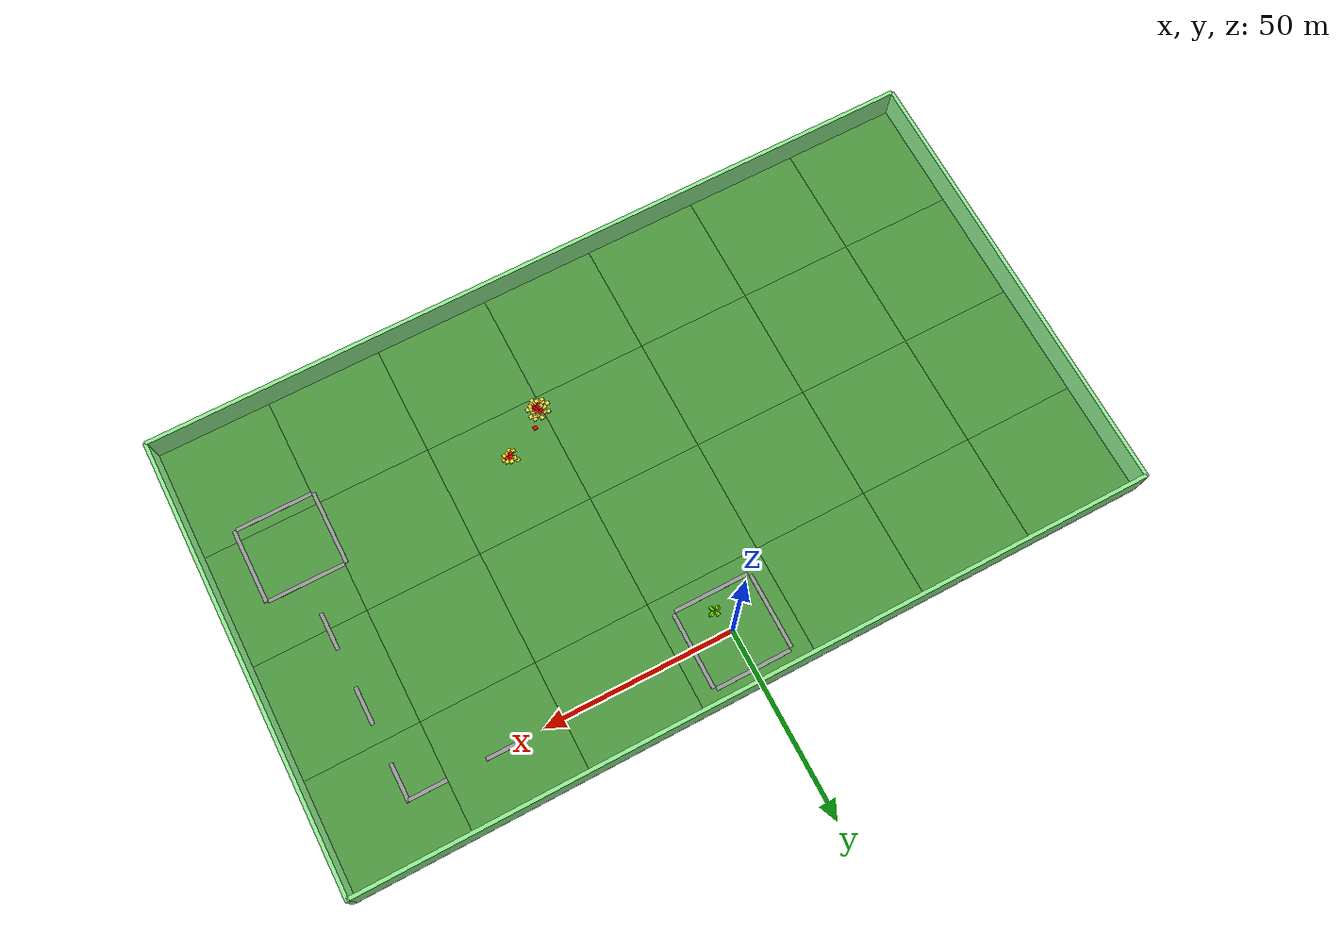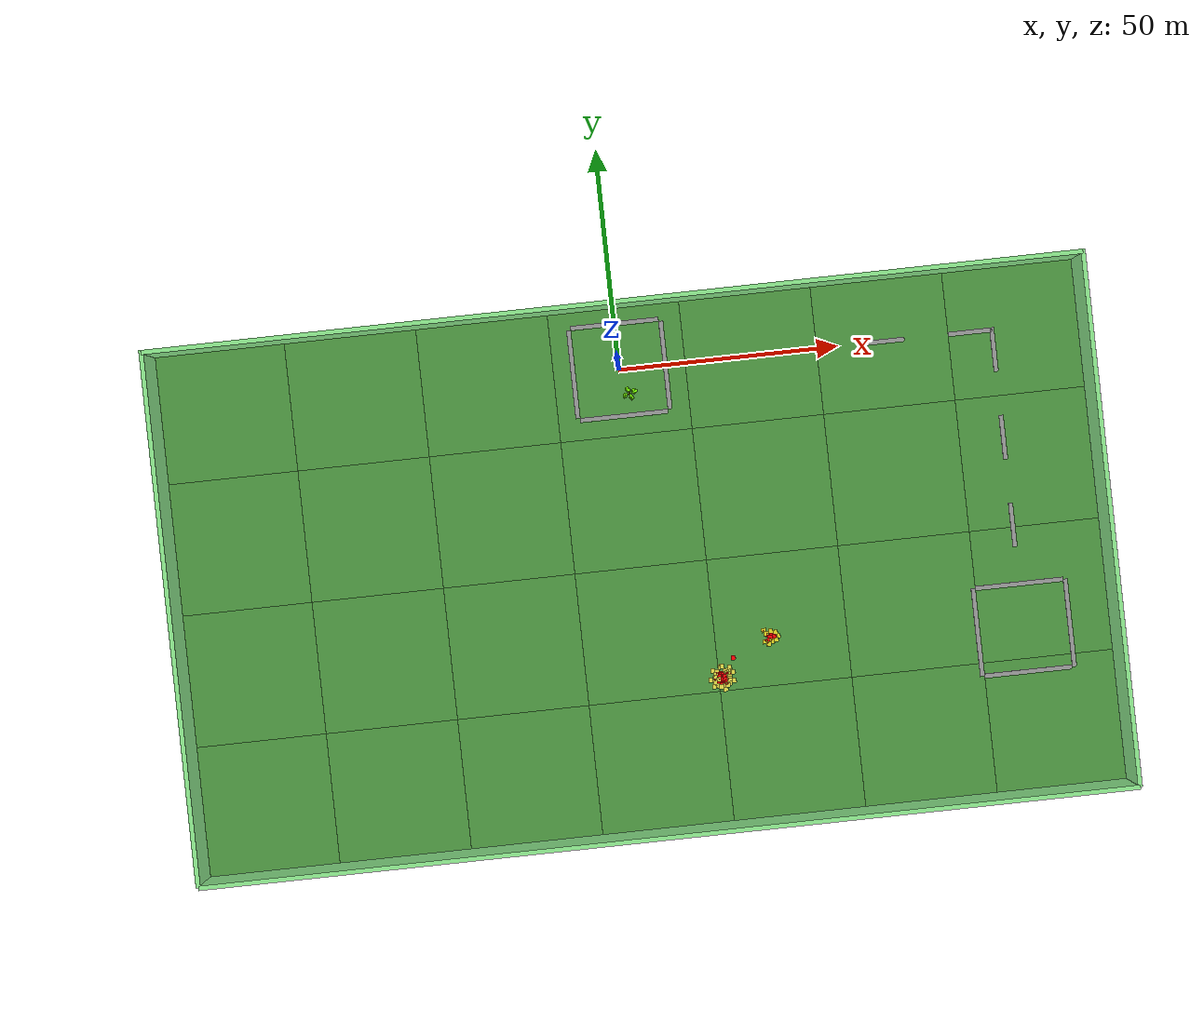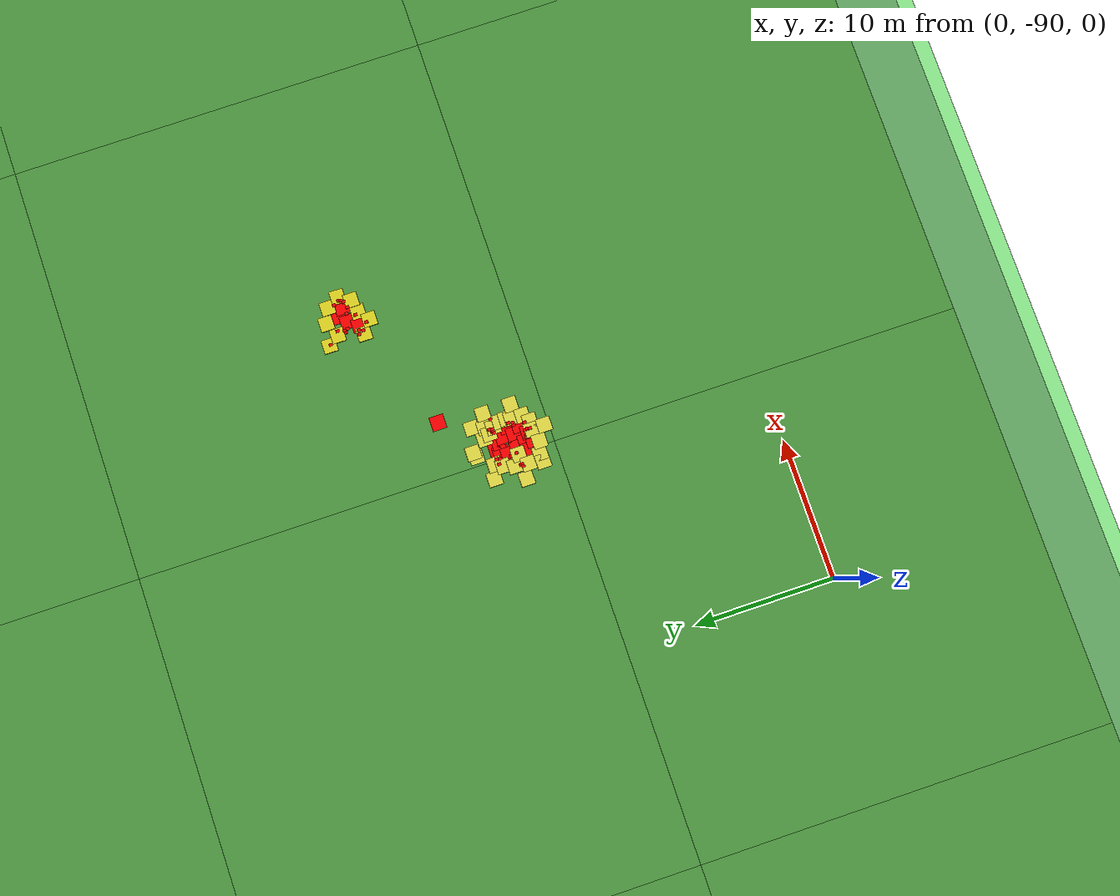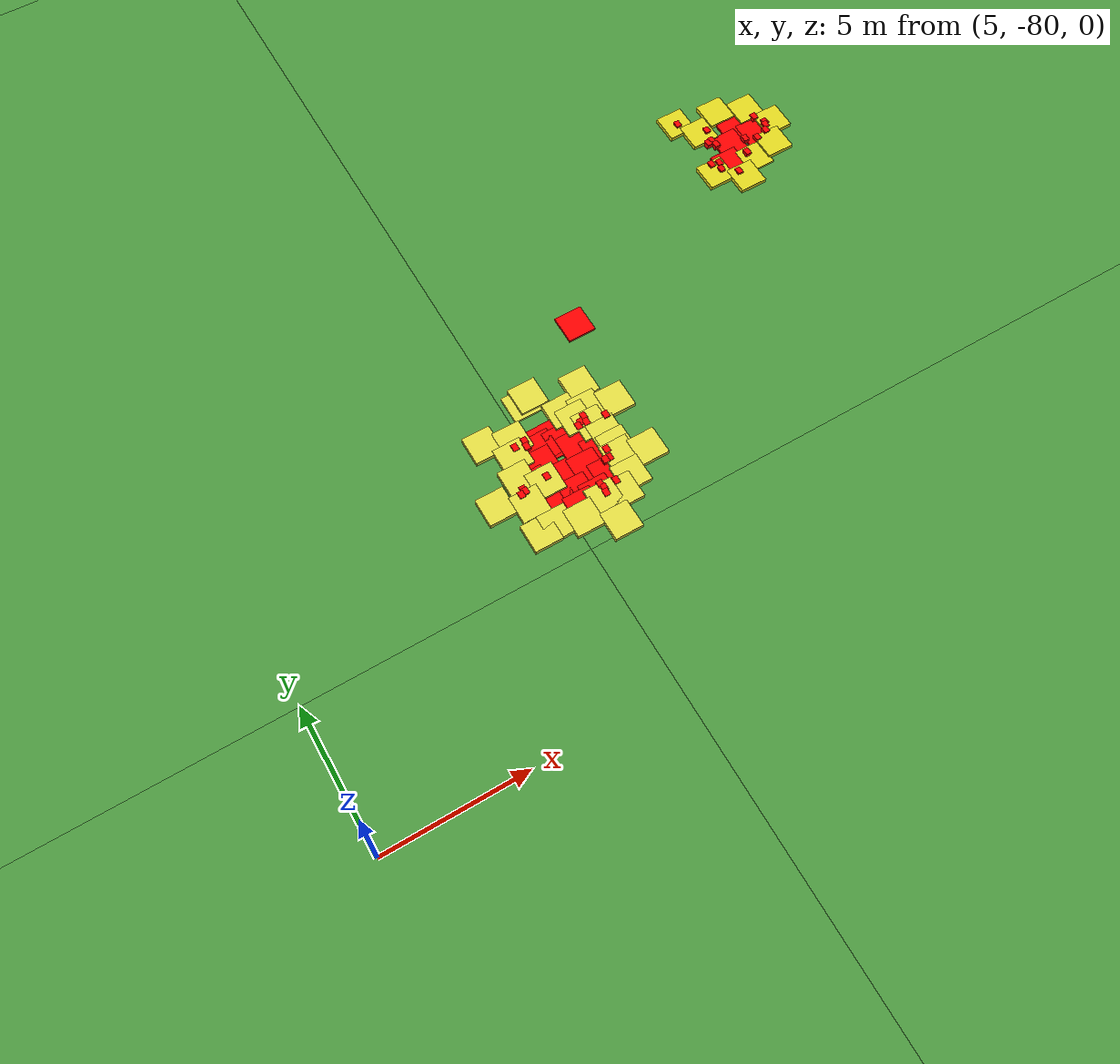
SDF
<sdf version="1.4">
 <world name="default">
  <scene>
   <sky><clouds><speed>12</speed></clouds></sky>
   <ambient>0.4 0.4 0.4 1</ambient>
   <background>0.7 0.7 0.7 1</background>
   <shadows>0</shadows>
  </scene>
  <include><uri>model://sun</uri></include>
  <include><uri>model://grass_plane</uri></include>
  <model name="tree 2">
   <static>1</static>
   <link name="link">
    <collision name="collision">
     <geometry><mesh><uri>model://tree2/meshes/tree2.dae</uri><scale>0.1 0.1 0.1</scale></mesh></geometry>
    </collision>
    <visual name="visual">
     <cast_shadows>false</cast_shadows>
     <geometry><mesh><uri>model://tree2/meshes/tree2.dae</uri><scale>0.1 0.1 0.1</scale></mesh></geometry>
    </visual>
   </link>
   <pose>0.774443 -3.93953 0 0 0 -1.20756</pose>
  </model>
  <model name="fire_box_clone">
   <link name="link">
    <inertial>
     <mass>1</mass>
     <inertia>
      <ixx>0.166667</ixx>
      <ixy>0</ixy>
      <ixz>0</ixz>
      <iyy>0.166667</iyy>
      <iyz>0</iyz>
      <izz>0.166667</izz>
     </inertia>
    </inertial>
    <visual name="visual">
     <geometry><box><size>1 1 0.2</size></box></geometry>
     <material>
      <script><name>Gazebo/Grey</name><uri>file://media/materials/scripts/gazebo.material</uri></script>
      <ambient>1 0 0 1</ambient>
      <diffuse>1 0 0 1</diffuse>
      <specular>0.01 0.01 0.01 1</specular>
      <emissive>0 0 0 1</emissive>
      <shader type="vertex"><normal_map>__default__</normal_map></shader>
      <lighting>1</lighting>
     </material>
    </visual>
   </link>
   <static>1</static>
   <pose>15.7226 -70.9882 -0.000684 2e-05 -0 5.1e-05</pose>
  </model>
  <model name="fire_box_clone_0">
   <link name="link">
    <inertial>
     <mass>1</mass>
     <inertia>
      <ixx>0.166667</ixx>
      <ixy>0</ixy>
      <ixz>0</ixz>
      <iyy>0.166667</iyy>
      <iyz>0</iyz>
      <izz>0.166667</izz>
     </inertia>
    </inertial>
    <visual name="visual">
     <geometry><box><size>1 1 0.2</size></box></geometry>
     <material>
      <script><name>Gazebo/Grey</name><uri>file://media/materials/scripts/gazebo.material</uri></script>
      <ambient>1 0 0 1</ambient>
      <diffuse>1 0 0 1</diffuse>
      <specular>0.01 0.01 0.01 1</specular>
      <emissive>0 0 0 1</emissive>
      <shader type="vertex"><normal_map>__default__</normal_map></shader>
      <lighting>1</lighting>
     </material>
    </visual>
   </link>
   <static>1</static>
   <pose>15.4112 -71.1872 -0.000684 2e-05 -0 5.1e-05</pose>
  </model>
  <model name="fire_box_clone_1">
   <link name="link">
    <inertial>
     <mass>1</mass>
     <inertia>
      <ixx>0.166667</ixx>
      <ixy>0</ixy>
      <ixz>0</ixz>
      <iyy>0.166667</iyy>
      <iyz>0</iyz>
      <izz>0.166667</izz>
     </inertia>
    </inertial>
    <visual name="visual">
     <geometry><box><size>1 1 0.2</size></box></geometry>
     <material>
      <script><name>Gazebo/Grey</name><uri>file://media/materials/scripts/gazebo.material</uri></script>
      <ambient>1 0 0 1</ambient>
      <diffuse>1 0 0 1</diffuse>
      <specular>0.01 0.01 0.01 1</specular>
      <emissive>0 0 0 1</emissive>
      <shader type="vertex"><normal_map>__default__</normal_map></shader>
      <lighting>1</lighting>
     </material>
    </visual>
   </link>
   <static>1</static>
   <pose>15.1356 -71.6886 -0.000684 2e-05 -0 5.1e-05</pose>
  </model>
  <model name="fire_box_clone_2">
   <link name="link">
    <inertial>
     <mass>1</mass>
     <inertia>
      <ixx>0.166667</ixx>
      <ixy>0</ixy>
      <ixz>0</ixz>
      <iyy>0.166667</iyy>
      <iyz>0</iyz>
      <izz>0.166667</izz>
     </inertia>
    </inertial>
    <visual name="visual">
     <geometry><box><size>1 1 0.2</size></box></geometry>
     <material>
      <script><name>Gazebo/Grey</name><uri>file://media/materials/scripts/gazebo.material</uri></script>
      <ambient>1 0 0 1</ambient>
      <diffuse>1 0 0 1</diffuse>
      <specular>0.01 0.01 0.01 1</specular>
      <emissive>0 0 0 1</emissive>
      <shader type="vertex"><normal_map>__default__</normal_map></shader>
      <lighting>1</lighting>
     </material>
    </visual>
   </link>
   <static>1</static>
   <pose>14.5844 -72.2161 -0.000684 2e-05 -0 5.1e-05</pose>
  </model>
  <model name="fire_box_clone_3">
   <link name="link">
    <inertial>
     <mass>1</mass>
     <inertia>
      <ixx>0.166667</ixx>
      <ixy>0</ixy>
      <ixz>0</ixz>
      <iyy>0.166667</iyy>
      <iyz>0</iyz>
      <izz>0.166667</izz>
     </inertia>
    </inertial>
    <visual name="visual">
     <geometry><box><size>1 1 0.2</size></box></geometry>
     <material>
      <script><name>Gazebo/Grey</name><uri>file://media/materials/scripts/gazebo.material</uri></script>
      <ambient>1 0 0 1</ambient>
      <diffuse>1 0 0 1</diffuse>
      <specular>0.01 0.01 0.01 1</specular>
      <emissive>0 0 0 1</emissive>
      <shader type="vertex"><normal_map>__default__</normal_map></shader>
      <lighting>1</lighting>
     </material>
    </visual>
   </link>
   <static>1</static>
   <pose>15.4097 -72.4161 -0.000684 2e-05 -0 5.1e-05</pose>
  </model>
  <model name="fire_box_clone_4">
   <link name="link">
    <inertial>
     <mass>1</mass>
     <inertia>
      <ixx>0.166667</ixx>
      <ixy>0</ixy>
      <ixz>0</ixz>
      <iyy>0.166667</iyy>
      <iyz>0</iyz>
      <izz>0.166667</izz>
     </inertia>
    </inertial>
    <visual name="visual">
     <geometry><box><size>1 1 0.2</size></box></geometry>
     <material>
      <script><name>Gazebo/Grey</name><uri>file://media/materials/scripts/gazebo.material</uri></script>
      <ambient>1 0 0 1</ambient>
      <diffuse>1 0 0 1</diffuse>
      <specular>0.01 0.01 0.01 1</specular>
      <emissive>0 0 0 1</emissive>
      <shader type="vertex"><normal_map>__default__</normal_map></shader>
      <lighting>1</lighting>
     </material>
    </visual>
   </link>
   <static>1</static>
   <pose>15.0003 -73.1414 -0.000684 2e-05 -0 5.1e-05</pose>
  </model>
  <model name="fire_box_clone_5">
   <link name="link">
    <inertial>
     <mass>1</mass>
     <inertia>
      <ixx>0.166667</ixx>
      <ixy>0</ixy>
      <ixz>0</ixz>
      <iyy>0.166667</iyy>
      <iyz>0</iyz>
      <izz>0.166667</izz>
     </inertia>
    </inertial>
    <visual name="visual">
     <geometry><box><size>1 1 0.2</size></box></geometry>
     <material>
      <script><name>Gazebo/Grey</name><uri>file://media/materials/scripts/gazebo.material</uri></script>
      <ambient>1 0 0 1</ambient>
      <diffuse>1 0 0 1</diffuse>
      <specular>0.01 0.01 0.01 1</specular>
      <emissive>0 0 0 1</emissive>
      <shader type="vertex"><normal_map>__default__</normal_map></shader>
      <lighting>1</lighting>
     </material>
    </visual>
   </link>
   <static>1</static>
   <pose>15.6299 -73.0916 -0.000684 2e-05 -0 5.1e-05</pose>
  </model>
  <model name="fire_box_clone_6">
   <link name="link">
    <inertial>
     <mass>1</mass>
     <inertia>
      <ixx>0.166667</ixx>
      <ixy>0</ixy>
      <ixz>0</ixz>
      <iyy>0.166667</iyy>
      <iyz>0</iyz>
      <izz>0.166667</izz>
     </inertia>
    </inertial>
    <visual name="visual">
     <geometry><box><size>1 1 0.2</size></box></geometry>
     <material>
      <script><name>Gazebo/Grey</name><uri>file://media/materials/scripts/gazebo.material</uri></script>
      <ambient>1 0 0 1</ambient>
      <diffuse>1 0 0 1</diffuse>
      <specular>0.01 0.01 0.01 1</specular>
      <emissive>0 0 0 1</emissive>
      <shader type="vertex"><normal_map>__default__</normal_map></shader>
      <lighting>1</lighting>
     </material>
    </visual>
   </link>
   <static>1</static>
   <pose>15.5499 -73.6027 -0.000684 2e-05 -0 5.1e-05</pose>
  </model>
  <model name="fire_box_clone_7">
   <link name="link">
    <inertial>
     <mass>1</mass>
     <inertia>
      <ixx>0.166667</ixx>
      <ixy>0</ixy>
      <ixz>0</ixz>
      <iyy>0.166667</iyy>
      <iyz>0</iyz>
      <izz>0.166667</izz>
     </inertia>
    </inertial>
    <visual name="visual">
     <geometry><box><size>1 1 0.2</size></box></geometry>
     <material>
      <script><name>Gazebo/Grey</name><uri>file://media/materials/scripts/gazebo.material</uri></script>
      <ambient>1 0 0 1</ambient>
      <diffuse>1 0 0 1</diffuse>
      <specular>0.01 0.01 0.01 1</specular>
      <emissive>0 0 0 1</emissive>
      <shader type="vertex"><normal_map>__default__</normal_map></shader>
      <lighting>1</lighting>
     </material>
    </visual>
   </link>
   <static>1</static>
   <pose>16.2003 -73.4699 -0.000684 2e-05 -0 5.1e-05</pose>
  </model>
  <model name="fire_box_clone_8">
   <link name="link">
    <inertial>
     <mass>1</mass>
     <inertia>
      <ixx>0.166667</ixx>
      <ixy>0</ixy>
      <ixz>0</ixz>
      <iyy>0.166667</iyy>
      <iyz>0</iyz>
      <izz>0.166667</izz>
     </inertia>
    </inertial>
    <visual name="visual">
     <geometry><box><size>1 1 0.2</size></box></geometry>
     <material>
      <script><name>Gazebo/Grey</name><uri>file://media/materials/scripts/gazebo.material</uri></script>
      <ambient>1 0 0 1</ambient>
      <diffuse>1 0 0 1</diffuse>
      <specular>0.01 0.01 0.01 1</specular>
      <emissive>0 0 0 1</emissive>
      <shader type="vertex"><normal_map>__default__</normal_map></shader>
      <lighting>1</lighting>
     </material>
    </visual>
   </link>
   <static>1</static>
   <pose>16.3414 -72.487 -0.000684 2e-05 -0 5.1e-05</pose>
  </model>
  <model name="fire_box_clone_9">
   <link name="link">
    <inertial>
     <mass>1</mass>
     <inertia>
      <ixx>0.166667</ixx>
      <ixy>0</ixy>
      <ixz>0</ixz>
      <iyy>0.166667</iyy>
      <iyz>0</iyz>
      <izz>0.166667</izz>
     </inertia>
    </inertial>
    <visual name="visual">
     <geometry><box><size>1 1 0.2</size></box></geometry>
     <material>
      <script><name>Gazebo/Grey</name><uri>file://media/materials/scripts/gazebo.material</uri></script>
      <ambient>1 0 0 1</ambient>
      <diffuse>1 0 0 1</diffuse>
      <specular>0.01 0.01 0.01 1</specular>
      <emissive>0 0 0 1</emissive>
      <shader type="vertex"><normal_map>__default__</normal_map></shader>
      <lighting>1</lighting>
     </material>
    </visual>
   </link>
   <static>1</static>
   <pose>16.8176 -72.9935 -0.000684 2e-05 -0 5.1e-05</pose>
  </model>
  <model name="fire_box_clone_10">
   <link name="link">
    <inertial>
     <mass>1</mass>
     <inertia>
      <ixx>0.166667</ixx>
      <ixy>0</ixy>
      <ixz>0</ixz>
      <iyy>0.166667</iyy>
      <iyz>0</iyz>
      <izz>0.166667</izz>
     </inertia>
    </inertial>
    <visual name="visual">
     <geometry><box><size>1 1 0.2</size></box></geometry>
     <material>
      <script><name>Gazebo/Grey</name><uri>file://media/materials/scripts/gazebo.material</uri></script>
      <ambient>1 0 0 1</ambient>
      <diffuse>1 0 0 1</diffuse>
      <specular>0.01 0.01 0.01 1</specular>
      <emissive>0 0 0 1</emissive>
      <shader type="vertex"><normal_map>__default__</normal_map></shader>
      <lighting>1</lighting>
     </material>
    </visual>
   </link>
   <static>1</static>
   <pose>16.4107 -71.6799 -0.000684 2e-05 -0 5.1e-05</pose>
  </model>
  <model name="fire_box_clone_11">
   <link name="link">
    <inertial>
     <mass>1</mass>
     <inertia>
      <ixx>0.166667</ixx>
      <ixy>0</ixy>
      <ixz>0</ixz>
      <iyy>0.166667</iyy>
      <iyz>0</iyz>
      <izz>0.166667</izz>
     </inertia>
    </inertial>
    <visual name="visual">
     <geometry><box><size>1 1 0.2</size></box></geometry>
     <material>
      <script><name>Gazebo/Grey</name><uri>file://media/materials/scripts/gazebo.material</uri></script>
      <ambient>1 0 0 1</ambient>
      <diffuse>1 0 0 1</diffuse>
      <specular>0.01 0.01 0.01 1</specular>
      <emissive>0 0 0 1</emissive>
      <shader type="vertex"><normal_map>__default__</normal_map></shader>
      <lighting>1</lighting>
     </material>
    </visual>
   </link>
   <static>1</static>
   <pose>17.0084 -72.1536 -0.000684 2e-05 -0 5.1e-05</pose>
  </model>
  <model name="fire_box_clone_12">
   <link name="link">
    <inertial>
     <mass>1</mass>
     <inertia>
      <ixx>0.166667</ixx>
      <ixy>0</ixy>
      <ixz>0</ixz>
      <iyy>0.166667</iyy>
      <iyz>0</iyz>
      <izz>0.166667</izz>
     </inertia>
    </inertial>
    <visual name="visual">
     <geometry><box><size>1 1 0.2</size></box></geometry>
     <material>
      <script><name>Gazebo/Grey</name><uri>file://media/materials/scripts/gazebo.material</uri></script>
      <ambient>1 0 0 1</ambient>
      <diffuse>1 0 0 1</diffuse>
      <specular>0.01 0.01 0.01 1</specular>
      <emissive>0 0 0 1</emissive>
      <shader type="vertex"><normal_map>__default__</normal_map></shader>
      <lighting>1</lighting>
     </material>
    </visual>
   </link>
   <static>1</static>
   <pose>16.1418 -71.2916 -0.000684 2e-05 -0 5.1e-05</pose>
  </model>
  <model name="fire_box_2">
   <link name="link">
    <inertial>
     <mass>1</mass>
     <inertia>
      <ixx>0.166667</ixx>
      <ixy>0</ixy>
      <ixz>0</ixz>
      <iyy>0.166667</iyy>
      <iyz>0</iyz>
      <izz>0.166667</izz>
     </inertia>
    </inertial>
    <visual name="visual">
     <geometry><box><size>1 1 0.2</size></box></geometry>
     <material>
      <script><name>Gazebo/Grey</name><uri>file://media/materials/scripts/gazebo.material</uri></script>
      <ambient>0.9 0.87 0.27 1</ambient>
      <diffuse>0.9 0.87 0.27 1</diffuse>
      <specular>0.01 0.01 0.01 1</specular>
      <emissive>0 0 0 1</emissive>
      <shader type="vertex"><normal_map>__default__</normal_map></shader>
      <lighting>1</lighting>
     </material>
    </visual>
   </link>
   <static>1</static>
   <pose>15.6571 -69.5171 -0.000684 2e-05 -0 5.1e-05</pose>
  </model>
  <model name="fire_box_2_clone">
   <link name="link">
    <inertial>
     <mass>1</mass>
     <inertia>
      <ixx>0.166667</ixx>
      <ixy>0</ixy>
      <ixz>0</ixz>
      <iyy>0.166667</iyy>
      <iyz>0</iyz>
      <izz>0.166667</izz>
     </inertia>
    </inertial>
    <visual name="visual">
     <geometry><box><size>1 1 0.2</size></box></geometry>
     <material>
      <script><name>Gazebo/Grey</name><uri>file://media/materials/scripts/gazebo.material</uri></script>
      <ambient>0.9 0.87 0.27 1</ambient>
      <diffuse>0.9 0.87 0.27 1</diffuse>
      <specular>0.01 0.01 0.01 1</specular>
      <emissive>0 0 0 1</emissive>
      <shader type="vertex"><normal_map>__default__</normal_map></shader>
      <lighting>1</lighting>
     </material>
    </visual>
   </link>
   <static>1</static>
   <pose>14.733 -70.5461 0.103208 2e-05 -0 5.1e-05</pose>
  </model>
  <model name="fire_box_2_clone_0">
   <link name="link">
    <inertial>
     <mass>1</mass>
     <inertia>
      <ixx>0.166667</ixx>
      <ixy>0</ixy>
      <ixz>0</ixz>
      <iyy>0.166667</iyy>
      <iyz>0</iyz>
      <izz>0.166667</izz>
     </inertia>
    </inertial>
    <visual name="visual">
     <geometry><box><size>1 1 0.2</size></box></geometry>
     <material>
      <script><name>Gazebo/Grey</name><uri>file://media/materials/scripts/gazebo.material</uri></script>
      <ambient>0.9 0.87 0.27 1</ambient>
      <diffuse>0.9 0.87 0.27 1</diffuse>
      <specular>0.01 0.01 0.01 1</specular>
      <emissive>0 0 0 1</emissive>
      <shader type="vertex"><normal_map>__default__</normal_map></shader>
      <lighting>1</lighting>
     </material>
    </visual>
   </link>
   <static>1</static>
   <pose>14.4584 -71.0804 0.103208 2e-05 -0 5.1e-05</pose>
  </model>
  <model name="fire_box_2_clone_1">
   <link name="link">
    <inertial>
     <mass>1</mass>
     <inertia>
      <ixx>0.166667</ixx>
      <ixy>0</ixy>
      <ixz>0</ixz>
      <iyy>0.166667</iyy>
      <iyz>0</iyz>
      <izz>0.166667</izz>
     </inertia>
    </inertial>
    <visual name="visual">
     <geometry><box><size>1 1 0.2</size></box></geometry>
     <material>
      <script><name>Gazebo/Grey</name><uri>file://media/materials/scripts/gazebo.material</uri></script>
      <ambient>0.9 0.87 0.27 1</ambient>
      <diffuse>0.9 0.87 0.27 1</diffuse>
      <specular>0.01 0.01 0.01 1</specular>
      <emissive>0 0 0 1</emissive>
      <shader type="vertex"><normal_map>__default__</normal_map></shader>
      <lighting>1</lighting>
     </material>
    </visual>
   </link>
   <static>1</static>
   <pose>13.8143 -70.2366 0.103208 2e-05 -0 5.1e-05</pose>
  </model>
  <model name="fire_box_2_clone_2">
   <link name="link">
    <inertial>
     <mass>1</mass>
     <inertia>
      <ixx>0.166667</ixx>
      <ixy>0</ixy>
      <ixz>0</ixz>
      <iyy>0.166667</iyy>
      <iyz>0</iyz>
      <izz>0.166667</izz>
     </inertia>
    </inertial>
    <visual name="visual">
     <geometry><box><size>1 1 0.2</size></box></geometry>
     <material>
      <script><name>Gazebo/Grey</name><uri>file://media/materials/scripts/gazebo.material</uri></script>
      <ambient>0.9 0.87 0.27 1</ambient>
      <diffuse>0.9 0.87 0.27 1</diffuse>
      <specular>0.01 0.01 0.01 1</specular>
      <emissive>0 0 0 1</emissive>
      <shader type="vertex"><normal_map>__default__</normal_map></shader>
      <lighting>1</lighting>
     </material>
    </visual>
   </link>
   <static>1</static>
   <pose>14.2088 -71.8443 0.103208 2e-05 -0 5.1e-05</pose>
  </model>
  <model name="fire_box_2_clone_3">
   <link name="link">
    <inertial>
     <mass>1</mass>
     <inertia>
      <ixx>0.166667</ixx>
      <ixy>0</ixy>
      <ixz>0</ixz>
      <iyy>0.166667</iyy>
      <iyz>0</iyz>
      <izz>0.166667</izz>
     </inertia>
    </inertial>
    <visual name="visual">
     <geometry><box><size>1 1 0.2</size></box></geometry>
     <material>
      <script><name>Gazebo/Grey</name><uri>file://media/materials/scripts/gazebo.material</uri></script>
      <ambient>0.9 0.87 0.27 1</ambient>
      <diffuse>0.9 0.87 0.27 1</diffuse>
      <specular>0.01 0.01 0.01 1</specular>
      <emissive>0 0 0 1</emissive>
      <shader type="vertex"><normal_map>__default__</normal_map></shader>
      <lighting>1</lighting>
     </material>
    </visual>
   </link>
   <static>1</static>
   <pose>14.0911 -72.7814 0.103208 2e-05 -0 5.1e-05</pose>
  </model>
  <model name="fire_box_2_clone_4">
   <link name="link">
    <inertial>
     <mass>1</mass>
     <inertia>
      <ixx>0.166667</ixx>
      <ixy>0</ixy>
      <ixz>0</ixz>
      <iyy>0.166667</iyy>
      <iyz>0</iyz>
      <izz>0.166667</izz>
     </inertia>
    </inertial>
    <visual name="visual">
     <geometry><box><size>1 1 0.2</size></box></geometry>
     <material>
      <script><name>Gazebo/Grey</name><uri>file://media/materials/scripts/gazebo.material</uri></script>
      <ambient>0.9 0.87 0.27 1</ambient>
      <diffuse>0.9 0.87 0.27 1</diffuse>
      <specular>0.01 0.01 0.01 1</specular>
      <emissive>0 0 0 1</emissive>
      <shader type="vertex"><normal_map>__default__</normal_map></shader>
      <lighting>1</lighting>
     </material>
    </visual>
   </link>
   <static>1</static>
   <pose>14.9046 -72.3438 0.103208 2e-05 -0 5.1e-05</pose>
  </model>
  <model name="fire_box_2_clone_5">
   <link name="link">
    <inertial>
     <mass>1</mass>
     <inertia>
      <ixx>0.166667</ixx>
      <ixy>0</ixy>
      <ixz>0</ixz>
      <iyy>0.166667</iyy>
      <iyz>0</iyz>
      <izz>0.166667</izz>
     </inertia>
    </inertial>
    <visual name="visual">
     <geometry><box><size>1 1 0.2</size></box></geometry>
     <material>
      <script><name>Gazebo/Grey</name><uri>file://media/materials/scripts/gazebo.material</uri></script>
      <ambient>0.9 0.87 0.27 1</ambient>
      <diffuse>0.9 0.87 0.27 1</diffuse>
      <specular>0.01 0.01 0.01 1</specular>
      <emissive>0 0 0 1</emissive>
      <shader type="vertex"><normal_map>__default__</normal_map></shader>
      <lighting>1</lighting>
     </material>
    </visual>
   </link>
   <static>1</static>
   <pose>14.5101 -73.7734 0.103208 2e-05 -0 5.1e-05</pose>
  </model>
  <model name="fire_box_2_clone_6">
   <link name="link">
    <inertial>
     <mass>1</mass>
     <inertia>
      <ixx>0.166667</ixx>
      <ixy>0</ixy>
      <ixz>0</ixz>
      <iyy>0.166667</iyy>
      <iyz>0</iyz>
      <izz>0.166667</izz>
     </inertia>
    </inertial>
    <visual name="visual">
     <geometry><box><size>1 1 0.2</size></box></geometry>
     <material>
      <script><name>Gazebo/Grey</name><uri>file://media/materials/scripts/gazebo.material</uri></script>
      <ambient>0.9 0.87 0.27 1</ambient>
      <diffuse>0.9 0.87 0.27 1</diffuse>
      <specular>0.01 0.01 0.01 1</specular>
      <emissive>0 0 0 1</emissive>
      <shader type="vertex"><normal_map>__default__</normal_map></shader>
      <lighting>1</lighting>
     </material>
    </visual>
   </link>
   <static>1</static>
   <pose>15.3292 -74.0074 0.103208 2e-05 -0 5.1e-05</pose>
  </model>
  <model name="fire_box_2_clone_7">
   <link name="link">
    <inertial>
     <mass>1</mass>
     <inertia>
      <ixx>0.166667</ixx>
      <ixy>0</ixy>
      <ixz>0</ixz>
      <iyy>0.166667</iyy>
      <iyz>0</iyz>
      <izz>0.166667</izz>
     </inertia>
    </inertial>
    <visual name="visual">
     <geometry><box><size>1 1 0.2</size></box></geometry>
     <material>
      <script><name>Gazebo/Grey</name><uri>file://media/materials/scripts/gazebo.material</uri></script>
      <ambient>0.9 0.87 0.27 1</ambient>
      <diffuse>0.9 0.87 0.27 1</diffuse>
      <specular>0.01 0.01 0.01 1</specular>
      <emissive>0 0 0 1</emissive>
      <shader type="vertex"><normal_map>__default__</normal_map></shader>
      <lighting>1</lighting>
     </material>
    </visual>
   </link>
   <static>1</static>
   <pose>17.5456 -72.2979 0.103208 2e-05 -0 5.1e-05</pose>
  </model>
  <model name="fire_box_2_clone_8">
   <link name="link">
    <inertial>
     <mass>1</mass>
     <inertia>
      <ixx>0.166667</ixx>
      <ixy>0</ixy>
      <ixz>0</ixz>
      <iyy>0.166667</iyy>
      <iyz>0</iyz>
      <izz>0.166667</izz>
     </inertia>
    </inertial>
    <visual name="visual">
     <geometry><box><size>1 1 0.2</size></box></geometry>
     <material>
      <script><name>Gazebo/Grey</name><uri>file://media/materials/scripts/gazebo.material</uri></script>
      <ambient>0.9 0.87 0.27 1</ambient>
      <diffuse>0.9 0.87 0.27 1</diffuse>
      <specular>0.01 0.01 0.01 1</specular>
      <emissive>0 0 0 1</emissive>
      <shader type="vertex"><normal_map>__default__</normal_map></shader>
      <lighting>1</lighting>
     </material>
    </visual>
   </link>
   <static>1</static>
   <pose>18.3683 -72.9005 0.103208 2e-05 -0 5.1e-05</pose>
  </model>
  <model name="fire_box_2_clone_9">
   <link name="link">
    <inertial>
     <mass>1</mass>
     <inertia>
      <ixx>0.166667</ixx>
      <ixy>0</ixy>
      <ixz>0</ixz>
      <iyy>0.166667</iyy>
      <iyz>0</iyz>
      <izz>0.166667</izz>
     </inertia>
    </inertial>
    <visual name="visual">
     <geometry><box><size>1 1 0.2</size></box></geometry>
     <material>
      <script><name>Gazebo/Grey</name><uri>file://media/materials/scripts/gazebo.material</uri></script>
      <ambient>0.9 0.87 0.27 1</ambient>
      <diffuse>0.9 0.87 0.27 1</diffuse>
      <specular>0.01 0.01 0.01 1</specular>
      <emissive>0 0 0 1</emissive>
      <shader type="vertex"><normal_map>__default__</normal_map></shader>
      <lighting>1</lighting>
     </material>
    </visual>
   </link>
   <static>1</static>
   <pose>17.3911 -73.4467 0.103208 2e-05 -0 5.1e-05</pose>
  </model>
  <model name="fire_box_2_clone_10">
   <link name="link">
    <inertial>
     <mass>1</mass>
     <inertia>
      <ixx>0.166667</ixx>
      <ixy>0</ixy>
      <ixz>0</ixz>
      <iyy>0.166667</iyy>
      <iyz>0</iyz>
      <izz>0.166667</izz>
     </inertia>
    </inertial>
    <visual name="visual">
     <geometry><box><size>1 1 0.2</size></box></geometry>
     <material>
      <script><name>Gazebo/Grey</name><uri>file://media/materials/scripts/gazebo.material</uri></script>
      <ambient>0.9 0.87 0.27 1</ambient>
      <diffuse>0.9 0.87 0.27 1</diffuse>
      <specular>0.01 0.01 0.01 1</specular>
      <emissive>0 0 0 1</emissive>
      <shader type="vertex"><normal_map>__default__</normal_map></shader>
      <lighting>1</lighting>
     </material>
    </visual>
   </link>
   <static>1</static>
   <pose>16.8702 -73.8257 0.103208 2e-05 -0 5.1e-05</pose>
  </model>
  <model name="fire_box_2_clone_11">
   <link name="link">
    <inertial>
     <mass>1</mass>
     <inertia>
      <ixx>0.166667</ixx>
      <ixy>0</ixy>
      <ixz>0</ixz>
      <iyy>0.166667</iyy>
      <iyz>0</iyz>
      <izz>0.166667</izz>
     </inertia>
    </inertial>
    <visual name="visual">
     <geometry><box><size>1 1 0.2</size></box></geometry>
     <material>
      <script><name>Gazebo/Grey</name><uri>file://media/materials/scripts/gazebo.material</uri></script>
      <ambient>0.9 0.87 0.27 1</ambient>
      <diffuse>0.9 0.87 0.27 1</diffuse>
      <specular>0.01 0.01 0.01 1</specular>
      <emissive>0 0 0 1</emissive>
      <shader type="vertex"><normal_map>__default__</normal_map></shader>
      <lighting>1</lighting>
     </material>
    </visual>
   </link>
   <static>1</static>
   <pose>16.2888 -74.6673 0.103208 2e-05 -0 5.1e-05</pose>
  </model>
  <model name="fire_box_2_clone_12">
   <link name="link">
    <inertial>
     <mass>1</mass>
     <inertia>
      <ixx>0.166667</ixx>
      <ixy>0</ixy>
      <ixz>0</ixz>
      <iyy>0.166667</iyy>
      <iyz>0</iyz>
      <izz>0.166667</izz>
     </inertia>
    </inertial>
    <visual name="visual">
     <geometry><box><size>1 1 0.2</size></box></geometry>
     <material>
      <script><name>Gazebo/Grey</name><uri>file://media/materials/scripts/gazebo.material</uri></script>
      <ambient>0.9 0.87 0.27 1</ambient>
      <diffuse>0.9 0.87 0.27 1</diffuse>
      <specular>0.01 0.01 0.01 1</specular>
      <emissive>0 0 0 1</emissive>
      <shader type="vertex"><normal_map>__default__</normal_map></shader>
      <lighting>1</lighting>
     </material>
    </visual>
   </link>
   <static>1</static>
   <pose>16.2505 -73.7442 0.103208 2e-05 -0 5.1e-05</pose>
  </model>
  <model name="fire_box_2_clone_13">
   <link name="link">
    <inertial>
     <mass>1</mass>
     <inertia>
      <ixx>0.166667</ixx>
      <ixy>0</ixy>
      <ixz>0</ixz>
      <iyy>0.166667</iyy>
      <iyz>0</iyz>
      <izz>0.166667</izz>
     </inertia>
    </inertial>
    <visual name="visual">
     <geometry><box><size>1 1 0.2</size></box></geometry>
     <material>
      <script><name>Gazebo/Grey</name><uri>file://media/materials/scripts/gazebo.material</uri></script>
      <ambient>0.9 0.87 0.27 1</ambient>
      <diffuse>0.9 0.87 0.27 1</diffuse>
      <specular>0.01 0.01 0.01 1</specular>
      <emissive>0 0 0 1</emissive>
      <shader type="vertex"><normal_map>__default__</normal_map></shader>
      <lighting>1</lighting>
     </material>
    </visual>
   </link>
   <static>1</static>
   <pose>17.4603 -72.6708 0.103208 2e-05 -0 5.1e-05</pose>
  </model>
  <model name="fire_box_2_clone_14">
   <link name="link">
    <inertial>
     <mass>1</mass>
     <inertia>
      <ixx>0.166667</ixx>
      <ixy>0</ixy>
      <ixz>0</ixz>
      <iyy>0.166667</iyy>
      <iyz>0</iyz>
      <izz>0.166667</izz>
     </inertia>
    </inertial>
    <visual name="visual">
     <geometry><box><size>1 1 0.2</size></box></geometry>
     <material>
      <script><name>Gazebo/Grey</name><uri>file://media/materials/scripts/gazebo.material</uri></script>
      <ambient>0.9 0.87 0.27 1</ambient>
      <diffuse>0.9 0.87 0.27 1</diffuse>
      <specular>0.01 0.01 0.01 1</specular>
      <emissive>0 0 0 1</emissive>
      <shader type="vertex"><normal_map>__default__</normal_map></shader>
      <lighting>1</lighting>
     </material>
    </visual>
   </link>
   <static>1</static>
   <pose>17.2442 -71.2753 0.103208 2e-05 -0 5.1e-05</pose>
  </model>
  <model name="fire_box_2_clone_15">
   <link name="link">
    <inertial>
     <mass>1</mass>
     <inertia>
      <ixx>0.166667</ixx>
      <ixy>0</ixy>
      <ixz>0</ixz>
      <iyy>0.166667</iyy>
      <iyz>0</iyz>
      <izz>0.166667</izz>
     </inertia>
    </inertial>
    <visual name="visual">
     <geometry><box><size>1 1 0.2</size></box></geometry>
     <material>
      <script><name>Gazebo/Grey</name><uri>file://media/materials/scripts/gazebo.material</uri></script>
      <ambient>0.9 0.87 0.27 1</ambient>
      <diffuse>0.9 0.87 0.27 1</diffuse>
      <specular>0.01 0.01 0.01 1</specular>
      <emissive>0 0 0 1</emissive>
      <shader type="vertex"><normal_map>__default__</normal_map></shader>
      <lighting>1</lighting>
     </material>
    </visual>
   </link>
   <static>1</static>
   <pose>16.6441 -70.4344 0.103208 2e-05 -0 5.1e-05</pose>
  </model>
  <model name="fire_box_2_clone_16">
   <link name="link">
    <inertial>
     <mass>1</mass>
     <inertia>
      <ixx>0.166667</ixx>
      <ixy>0</ixy>
      <ixz>0</ixz>
      <iyy>0.166667</iyy>
      <iyz>0</iyz>
      <izz>0.166667</izz>
     </inertia>
    </inertial>
    <visual name="visual">
     <geometry><box><size>1 1 0.2</size></box></geometry>
     <material>
      <script><name>Gazebo/Grey</name><uri>file://media/materials/scripts/gazebo.material</uri></script>
      <ambient>0.9 0.87 0.27 1</ambient>
      <diffuse>0.9 0.87 0.27 1</diffuse>
      <specular>0.01 0.01 0.01 1</specular>
      <emissive>0 0 0 1</emissive>
      <shader type="vertex"><normal_map>__default__</normal_map></shader>
      <lighting>1</lighting>
     </material>
    </visual>
   </link>
   <static>1</static>
   <pose>16.8791 -70.8578 0.103208 2e-05 -0 5.1e-05</pose>
  </model>
  <model name="fire_box_2_clone_17">
   <link name="link">
    <inertial>
     <mass>1</mass>
     <inertia>
      <ixx>0.166667</ixx>
      <ixy>0</ixy>
      <ixz>0</ixz>
      <iyy>0.166667</iyy>
      <iyz>0</iyz>
      <izz>0.166667</izz>
     </inertia>
    </inertial>
    <visual name="visual">
     <geometry><box><size>1 1 0.2</size></box></geometry>
     <material>
      <script><name>Gazebo/Grey</name><uri>file://media/materials/scripts/gazebo.material</uri></script>
      <ambient>0.9 0.87 0.27 1</ambient>
      <diffuse>0.9 0.87 0.27 1</diffuse>
      <specular>0.01 0.01 0.01 1</specular>
      <emissive>0 0 0 1</emissive>
      <shader type="vertex"><normal_map>__default__</normal_map></shader>
      <lighting>1</lighting>
     </material>
    </visual>
   </link>
   <static>1</static>
   <pose>17.4797 -71.8 0.103208 2e-05 -0 5.1e-05</pose>
  </model>
  <model name="fire_box_2_clone_18">
   <link name="link">
    <inertial>
     <mass>1</mass>
     <inertia>
      <ixx>0.166667</ixx>
      <ixy>0</ixy>
      <ixz>0</ixz>
      <iyy>0.166667</iyy>
      <iyz>0</iyz>
      <izz>0.166667</izz>
     </inertia>
    </inertial>
    <visual name="visual">
     <geometry><box><size>1 1 0.2</size></box></geometry>
     <material>
      <script><name>Gazebo/Grey</name><uri>file://media/materials/scripts/gazebo.material</uri></script>
      <ambient>0.9 0.87 0.27 1</ambient>
      <diffuse>0.9 0.87 0.27 1</diffuse>
      <specular>0.01 0.01 0.01 1</specular>
      <emissive>0 0 0 1</emissive>
      <shader type="vertex"><normal_map>__default__</normal_map></shader>
      <lighting>1</lighting>
     </material>
    </visual>
   </link>
   <static>1</static>
   <pose>17.4152 -70.6947 0.103208 2e-05 -0 5.1e-05</pose>
  </model>
  <model name="fire_box_2_clone_19">
   <link name="link">
    <inertial>
     <mass>1</mass>
     <inertia>
      <ixx>0.166667</ixx>
      <ixy>0</ixy>
      <ixz>0</ixz>
      <iyy>0.166667</iyy>
      <iyz>0</iyz>
      <izz>0.166667</izz>
     </inertia>
    </inertial>
    <visual name="visual">
     <geometry><box><size>1 1 0.2</size></box></geometry>
     <material>
      <script><name>Gazebo/Grey</name><uri>file://media/materials/scripts/gazebo.material</uri></script>
      <ambient>0.9 0.87 0.27 1</ambient>
      <diffuse>0.9 0.87 0.27 1</diffuse>
      <specular>0.01 0.01 0.01 1</specular>
      <emissive>0 0 0 1</emissive>
      <shader type="vertex"><normal_map>__default__</normal_map></shader>
      <lighting>1</lighting>
     </material>
    </visual>
   </link>
   <static>1</static>
   <pose>17.6368 -69.8387 0.103208 2e-05 -0 5.1e-05</pose>
  </model>
  <model name="fire_box_2_clone_20">
   <link name="link">
    <inertial>
     <mass>1</mass>
     <inertia>
      <ixx>0.166667</ixx>
      <ixy>0</ixy>
      <ixz>0</ixz>
      <iyy>0.166667</iyy>
      <iyz>0</iyz>
      <izz>0.166667</izz>
     </inertia>
    </inertial>
    <visual name="visual">
     <geometry><box><size>1 1 0.2</size></box></geometry>
     <material>
      <script><name>Gazebo/Grey</name><uri>file://media/materials/scripts/gazebo.material</uri></script>
      <ambient>0.9 0.87 0.27 1</ambient>
      <diffuse>0.9 0.87 0.27 1</diffuse>
      <specular>0.01 0.01 0.01 1</specular>
      <emissive>0 0 0 1</emissive>
      <shader type="vertex"><normal_map>__default__</normal_map></shader>
      <lighting>1</lighting>
     </material>
    </visual>
   </link>
   <static>1</static>
   <pose>18.3543 -70.8926 0.103208 2e-05 -0 5.1e-05</pose>
  </model>
  <model name="fire_box_2_clone_21">
   <link name="link">
    <inertial>
     <mass>1</mass>
     <inertia>
      <ixx>0.166667</ixx>
      <ixy>0</ixy>
      <ixz>0</ixz>
      <iyy>0.166667</iyy>
      <iyz>0</iyz>
      <izz>0.166667</izz>
     </inertia>
    </inertial>
    <visual name="visual">
     <geometry><box><size>1 1 0.2</size></box></geometry>
     <material>
      <script><name>Gazebo/Grey</name><uri>file://media/materials/scripts/gazebo.material</uri></script>
      <ambient>0.9 0.87 0.27 1</ambient>
      <diffuse>0.9 0.87 0.27 1</diffuse>
      <specular>0.01 0.01 0.01 1</specular>
      <emissive>0 0 0 1</emissive>
      <shader type="vertex"><normal_map>__default__</normal_map></shader>
      <lighting>1</lighting>
     </material>
    </visual>
   </link>
   <static>1</static>
   <pose>13.1379 -72.3336 0.103208 2e-05 -0 5.1e-05</pose>
  </model>
  <model name="fire_box_2_clone_22">
   <link name="link">
    <inertial>
     <mass>1</mass>
     <inertia>
      <ixx>0.166667</ixx>
      <ixy>0</ixy>
      <ixz>0</ixz>
      <iyy>0.166667</iyy>
      <iyz>0</iyz>
      <izz>0.166667</izz>
     </inertia>
    </inertial>
    <visual name="visual">
     <geometry><box><size>1 1 0.2</size></box></geometry>
     <material>
      <script><name>Gazebo/Grey</name><uri>file://media/materials/scripts/gazebo.material</uri></script>
      <ambient>0.9 0.87 0.27 1</ambient>
      <diffuse>0.9 0.87 0.27 1</diffuse>
      <specular>0.01 0.01 0.01 1</specular>
      <emissive>0 0 0 1</emissive>
      <shader type="vertex"><normal_map>__default__</normal_map></shader>
      <lighting>1</lighting>
     </material>
    </visual>
   </link>
   <static>1</static>
   <pose>13.9248 -73.7967 0.103208 2e-05 -0 5.1e-05</pose>
  </model>
  <model name="fire_box_2_clone_23">
   <link name="link">
    <inertial>
     <mass>1</mass>
     <inertia>
      <ixx>0.166667</ixx>
      <ixy>0</ixy>
      <ixz>0</ixz>
      <iyy>0.166667</iyy>
      <iyz>0</iyz>
      <izz>0.166667</izz>
     </inertia>
    </inertial>
    <visual name="visual">
     <geometry><box><size>1 1 0.2</size></box></geometry>
     <material>
      <script><name>Gazebo/Grey</name><uri>file://media/materials/scripts/gazebo.material</uri></script>
      <ambient>0.9 0.87 0.27 1</ambient>
      <diffuse>0.9 0.87 0.27 1</diffuse>
      <specular>0.01 0.01 0.01 1</specular>
      <emissive>0 0 0 1</emissive>
      <shader type="vertex"><normal_map>__default__</normal_map></shader>
      <lighting>1</lighting>
     </material>
    </visual>
   </link>
   <static>1</static>
   <pose>15.9631 -69.4026 0.103208 2e-05 -0 5.1e-05</pose>
  </model>
  <model name="fire_box_clone_10_clone">
   <link name="link">
    <inertial>
     <mass>1</mass>
     <inertia>
      <ixx>0.166667</ixx>
      <ixy>0</ixy>
      <ixz>0</ixz>
      <iyy>0.166667</iyy>
      <iyz>0</iyz>
      <izz>0.166667</izz>
     </inertia>
    </inertial>
    <visual name="visual">
     <geometry><box><size>1 1 0.2</size></box></geometry>
     <material>
      <script><name>Gazebo/Grey</name><uri>file://media/materials/scripts/gazebo.material</uri></script>
      <ambient>1 0 0 1</ambient>
      <diffuse>1 0 0 1</diffuse>
      <specular>0.01 0.01 0.01 1</specular>
      <emissive>0 0 0 1</emissive>
      <shader type="vertex"><normal_map>__default__</normal_map></shader>
      <lighting>1</lighting>
     </material>
    </visual>
   </link>
   <static>1</static>
   <pose>18.7374 -67.7575 -0.000684 2e-05 -0 5.1e-05</pose>
  </model>
  <model name="fire_box_clone_10_clone_clone">
   <link name="link">
    <inertial>
     <mass>1</mass>
     <inertia>
      <ixx>0.166667</ixx>
      <ixy>0</ixy>
      <ixz>0</ixz>
      <iyy>0.166667</iyy>
      <iyz>0</iyz>
      <izz>0.166667</izz>
     </inertia>
    </inertial>
    <visual name="visual">
     <geometry><box><size>0.205115 0.254942 0.2</size></box></geometry>
     <material>
      <script><name>Gazebo/Grey</name><uri>file://media/materials/scripts/gazebo.material</uri></script>
      <ambient>1 0 0 1</ambient>
      <diffuse>1 0 0 1</diffuse>
      <specular>0.01 0.01 0.01 1</specular>
      <emissive>0 0 0 1</emissive>
      <shader type="vertex"><normal_map>__default__</normal_map></shader>
      <lighting>1</lighting>
     </material>
    </visual>
   </link>
   <static>1</static>
   <pose>17.7918 -71.2662 0.142519 2e-05 -0 5.1e-05</pose>
  </model>
  <model name="fire_box_clone_10_clone_clone_0">
   <link name="link">
    <inertial>
     <mass>1</mass>
     <inertia>
      <ixx>0.166667</ixx>
      <ixy>0</ixy>
      <ixz>0</ixz>
      <iyy>0.166667</iyy>
      <iyz>0</iyz>
      <izz>0.166667</izz>
     </inertia>
    </inertial>
    <visual name="visual">
     <geometry><box><size>0.205115 0.254942 0.2</size></box></geometry>
     <material>
      <script><name>Gazebo/Grey</name><uri>file://media/materials/scripts/gazebo.material</uri></script>
      <ambient>1 0 0 1</ambient>
      <diffuse>1 0 0 1</diffuse>
      <specular>0.01 0.01 0.01 1</specular>
      <emissive>0 0 0 1</emissive>
      <shader type="vertex"><normal_map>__default__</normal_map></shader>
      <lighting>1</lighting>
     </material>
    </visual>
   </link>
   <static>1</static>
   <pose>16.8177 -71.187 0.142519 2e-05 -0 5.1e-05</pose>
  </model>
  <model name="fire_box_clone_10_clone_clone_1">
   <link name="link">
    <inertial>
     <mass>1</mass>
     <inertia>
      <ixx>0.166667</ixx>
      <ixy>0</ixy>
      <ixz>0</ixz>
      <iyy>0.166667</iyy>
      <iyz>0</iyz>
      <izz>0.166667</izz>
     </inertia>
    </inertial>
    <visual name="visual">
     <geometry><box><size>0.205115 0.254942 0.2</size></box></geometry>
     <material>
      <script><name>Gazebo/Grey</name><uri>file://media/materials/scripts/gazebo.material</uri></script>
      <ambient>1 0 0 1</ambient>
      <diffuse>1 0 0 1</diffuse>
      <specular>0.01 0.01 0.01 1</specular>
      <emissive>0 0 0 1</emissive>
      <shader type="vertex"><normal_map>__default__</normal_map></shader>
      <lighting>1</lighting>
     </material>
    </visual>
   </link>
   <static>1</static>
   <pose>17.107 -71.1758 0.142519 2e-05 -0 5.1e-05</pose>
  </model>
  <model name="fire_box_clone_10_clone_clone_2">
   <link name="link">
    <inertial>
     <mass>1</mass>
     <inertia>
      <ixx>0.166667</ixx>
      <ixy>0</ixy>
      <ixz>0</ixz>
      <iyy>0.166667</iyy>
      <iyz>0</iyz>
      <izz>0.166667</izz>
     </inertia>
    </inertial>
    <visual name="visual">
     <geometry><box><size>0.205115 0.254942 0.2</size></box></geometry>
     <material>
      <script><name>Gazebo/Grey</name><uri>file://media/materials/scripts/gazebo.material</uri></script>
      <ambient>1 0 0 1</ambient>
      <diffuse>1 0 0 1</diffuse>
      <specular>0.01 0.01 0.01 1</specular>
      <emissive>0 0 0 1</emissive>
      <shader type="vertex"><normal_map>__default__</normal_map></shader>
      <lighting>1</lighting>
     </material>
    </visual>
   </link>
   <static>1</static>
   <pose>16.945 -71.1063 0.142519 2e-05 -0 5.1e-05</pose>
  </model>
  <model name="fire_box_clone_10_clone_clone_3">
   <link name="link">
    <inertial>
     <mass>1</mass>
     <inertia>
      <ixx>0.166667</ixx>
      <ixy>0</ixy>
      <ixz>0</ixz>
      <iyy>0.166667</iyy>
      <iyz>0</iyz>
      <izz>0.166667</izz>
     </inertia>
    </inertial>
    <visual name="visual">
     <geometry><box><size>0.205115 0.254942 0.2</size></box></geometry>
     <material>
      <script><name>Gazebo/Grey</name><uri>file://media/materials/scripts/gazebo.material</uri></script>
      <ambient>1 0 0 1</ambient>
      <diffuse>1 0 0 1</diffuse>
      <specular>0.01 0.01 0.01 1</specular>
      <emissive>0 0 0 1</emissive>
      <shader type="vertex"><normal_map>__default__</normal_map></shader>
      <lighting>1</lighting>
     </material>
    </visual>
   </link>
   <static>1</static>
   <pose>17.139 -70.9635 0.142519 2e-05 -0 5.1e-05</pose>
  </model>
  <model name="fire_box_clone_10_clone_clone_4">
   <link name="link">
    <inertial>
     <mass>1</mass>
     <inertia>
      <ixx>0.166667</ixx>
      <ixy>0</ixy>
      <ixz>0</ixz>
      <iyy>0.166667</iyy>
      <iyz>0</iyz>
      <izz>0.166667</izz>
     </inertia>
    </inertial>
    <visual name="visual">
     <geometry><box><size>0.205115 0.254942 0.2</size></box></geometry>
     <material>
      <script><name>Gazebo/Grey</name><uri>file://media/materials/scripts/gazebo.material</uri></script>
      <ambient>1 0 0 1</ambient>
      <diffuse>1 0 0 1</diffuse>
      <specular>0.01 0.01 0.01 1</specular>
      <emissive>0 0 0 1</emissive>
      <shader type="vertex"><normal_map>__default__</normal_map></shader>
      <lighting>1</lighting>
     </material>
    </visual>
   </link>
   <static>1</static>
   <pose>14.0071 -72.3912 0.142519 2e-05 -0 5.1e-05</pose>
  </model>
  <model name="fire_box_clone_10_clone_clone_5">
   <link name="link">
    <inertial>
     <mass>1</mass>
     <inertia>
      <ixx>0.166667</ixx>
      <ixy>0</ixy>
      <ixz>0</ixz>
      <iyy>0.166667</iyy>
      <iyz>0</iyz>
      <izz>0.166667</izz>
     </inertia>
    </inertial>
    <visual name="visual">
     <geometry><box><size>0.205115 0.254942 0.2</size></box></geometry>
     <material>
      <script><name>Gazebo/Grey</name><uri>file://media/materials/scripts/gazebo.material</uri></script>
      <ambient>1 0 0 1</ambient>
      <diffuse>1 0 0 1</diffuse>
      <specular>0.01 0.01 0.01 1</specular>
      <emissive>0 0 0 1</emissive>
      <shader type="vertex"><normal_map>__default__</normal_map></shader>
      <lighting>1</lighting>
     </material>
    </visual>
   </link>
   <static>1</static>
   <pose>14.1765 -72.3442 0.142519 2e-05 -0 5.1e-05</pose>
  </model>
  <model name="fire_box_clone_10_clone_clone_6">
   <link name="link">
    <inertial>
     <mass>1</mass>
     <inertia>
      <ixx>0.166667</ixx>
      <ixy>0</ixy>
      <ixz>0</ixz>
      <iyy>0.166667</iyy>
      <iyz>0</iyz>
      <izz>0.166667</izz>
     </inertia>
    </inertial>
    <visual name="visual">
     <geometry><box><size>0.205115 0.254942 0.2</size></box></geometry>
     <material>
      <script><name>Gazebo/Grey</name><uri>file://media/materials/scripts/gazebo.material</uri></script>
      <ambient>1 0 0 1</ambient>
      <diffuse>1 0 0 1</diffuse>
      <specular>0.01 0.01 0.01 1</specular>
      <emissive>0 0 0 1</emissive>
      <shader type="vertex"><normal_map>__default__</normal_map></shader>
      <lighting>1</lighting>
     </material>
    </visual>
   </link>
   <static>1</static>
   <pose>14.142 -72.2617 0.142519 2e-05 -0 5.1e-05</pose>
  </model>
  <model name="fire_box_clone_10_clone_clone_7">
   <link name="link">
    <inertial>
     <mass>1</mass>
     <inertia>
      <ixx>0.166667</ixx>
      <ixy>0</ixy>
      <ixz>0</ixz>
      <iyy>0.166667</iyy>
      <iyz>0</iyz>
      <izz>0.166667</izz>
     </inertia>
    </inertial>
    <visual name="visual">
     <geometry><box><size>0.205115 0.254942 0.2</size></box></geometry>
     <material>
      <script><name>Gazebo/Grey</name><uri>file://media/materials/scripts/gazebo.material</uri></script>
      <ambient>1 0 0 1</ambient>
      <diffuse>1 0 0 1</diffuse>
      <specular>0.01 0.01 0.01 1</specular>
      <emissive>0 0 0 1</emissive>
      <shader type="vertex"><normal_map>__default__</normal_map></shader>
      <lighting>1</lighting>
     </material>
    </visual>
   </link>
   <static>1</static>
   <pose>14.6555 -70.8455 0.142519 2e-05 -0 5.1e-05</pose>
  </model>
  <model name="fire_box_clone_10_clone_clone_8">
   <link name="link">
    <inertial>
     <mass>1</mass>
     <inertia>
      <ixx>0.166667</ixx>
      <ixy>0</ixy>
      <ixz>0</ixz>
      <iyy>0.166667</iyy>
      <iyz>0</iyz>
      <izz>0.166667</izz>
     </inertia>
    </inertial>
    <visual name="visual">
     <geometry><box><size>0.205115 0.254942 0.2</size></box></geometry>
     <material>
      <script><name>Gazebo/Grey</name><uri>file://media/materials/scripts/gazebo.material</uri></script>
      <ambient>1 0 0 1</ambient>
      <diffuse>1 0 0 1</diffuse>
      <specular>0.01 0.01 0.01 1</specular>
      <emissive>0 0 0 1</emissive>
      <shader type="vertex"><normal_map>__default__</normal_map></shader>
      <lighting>1</lighting>
     </material>
    </visual>
   </link>
   <static>1</static>
   <pose>15.023 -72.2306 0.142519 2e-05 -0 5.1e-05</pose>
  </model>
  <model name="fire_box_clone_10_clone_clone_9">
   <link name="link">
    <inertial>
     <mass>1</mass>
     <inertia>
      <ixx>0.166667</ixx>
      <ixy>0</ixy>
      <ixz>0</ixz>
      <iyy>0.166667</iyy>
      <iyz>0</iyz>
      <izz>0.166667</izz>
     </inertia>
    </inertial>
    <visual name="visual">
     <geometry><box><size>0.205115 0.254942 0.2</size></box></geometry>
     <material>
      <script><name>Gazebo/Grey</name><uri>file://media/materials/scripts/gazebo.material</uri></script>
      <ambient>1 0 0 1</ambient>
      <diffuse>1 0 0 1</diffuse>
      <specular>0.01 0.01 0.01 1</specular>
      <emissive>0 0 0 1</emissive>
      <shader type="vertex"><normal_map>__default__</normal_map></shader>
      <lighting>1</lighting>
     </material>
    </visual>
   </link>
   <static>1</static>
   <pose>15.0374 -70.7943 0.142519 2e-05 -0 5.1e-05</pose>
  </model>
  <model name="fire_box_clone_10_clone_clone_10">
   <link name="link">
    <inertial>
     <mass>1</mass>
     <inertia>
      <ixx>0.166667</ixx>
      <ixy>0</ixy>
      <ixz>0</ixz>
      <iyy>0.166667</iyy>
      <iyz>0</iyz>
      <izz>0.166667</izz>
     </inertia>
    </inertial>
    <visual name="visual">
     <geometry><box><size>0.205115 0.254942 0.2</size></box></geometry>
     <material>
      <script><name>Gazebo/Grey</name><uri>file://media/materials/scripts/gazebo.material</uri></script>
      <ambient>1 0 0 1</ambient>
      <diffuse>1 0 0 1</diffuse>
      <specular>0.01 0.01 0.01 1</specular>
      <emissive>0 0 0 1</emissive>
      <shader type="vertex"><normal_map>__default__</normal_map></shader>
      <lighting>1</lighting>
     </material>
    </visual>
   </link>
   <static>1</static>
   <pose>15 -71 0.142519 2e-05 -0 5.1e-05</pose>
  </model>
  <model name="fire_box_clone_10_clone_clone_11">
   <link name="link">
    <inertial>
     <mass>1</mass>
     <inertia>
      <ixx>0.166667</ixx>
      <ixy>0</ixy>
      <ixz>0</ixz>
      <iyy>0.166667</iyy>
      <iyz>0</iyz>
      <izz>0.166667</izz>
     </inertia>
    </inertial>
    <visual name="visual">
     <geometry><box><size>0.205115 0.254942 0.2</size></box></geometry>
     <material>
      <script><name>Gazebo/Grey</name><uri>file://media/materials/scripts/gazebo.material</uri></script>
      <ambient>1 0 0 1</ambient>
      <diffuse>1 0 0 1</diffuse>
      <specular>0.01 0.01 0.01 1</specular>
      <emissive>0 0 0 1</emissive>
      <shader type="vertex"><normal_map>__default__</normal_map></shader>
      <lighting>1</lighting>
     </material>
    </visual>
   </link>
   <static>1</static>
   <pose>16.9391 -72.6447 0.142519 2e-05 -0 5.1e-05</pose>
  </model>
  <model name="fire_box_clone_10_clone_clone_12">
   <link name="link">
    <inertial>
     <mass>1</mass>
     <inertia>
      <ixx>0.166667</ixx>
      <ixy>0</ixy>
      <ixz>0</ixz>
      <iyy>0.166667</iyy>
      <iyz>0</iyz>
      <izz>0.166667</izz>
     </inertia>
    </inertial>
    <visual name="visual">
     <geometry><box><size>0.205115 0.254942 0.2</size></box></geometry>
     <material>
      <script><name>Gazebo/Grey</name><uri>file://media/materials/scripts/gazebo.material</uri></script>
      <ambient>1 0 0 1</ambient>
      <diffuse>1 0 0 1</diffuse>
      <specular>0.01 0.01 0.01 1</specular>
      <emissive>0 0 0 1</emissive>
      <shader type="vertex"><normal_map>__default__</normal_map></shader>
      <lighting>1</lighting>
     </material>
    </visual>
   </link>
   <static>1</static>
   <pose>17.0958 -72.6502 0.142519 2e-05 -0 5.1e-05</pose>
  </model>
  <model name="fire_box_clone_10_clone_clone_13">
   <link name="link">
    <inertial>
     <mass>1</mass>
     <inertia>
      <ixx>0.166667</ixx>
      <ixy>0</ixy>
      <ixz>0</ixz>
      <iyy>0.166667</iyy>
      <iyz>0</iyz>
      <izz>0.166667</izz>
     </inertia>
    </inertial>
    <visual name="visual">
     <geometry><box><size>0.205115 0.254942 0.2</size></box></geometry>
     <material>
      <script><name>Gazebo/Grey</name><uri>file://media/materials/scripts/gazebo.material</uri></script>
      <ambient>1 0 0 1</ambient>
      <diffuse>1 0 0 1</diffuse>
      <specular>0.01 0.01 0.01 1</specular>
      <emissive>0 0 0 1</emissive>
      <shader type="vertex"><normal_map>__default__</normal_map></shader>
      <lighting>1</lighting>
     </material>
    </visual>
   </link>
   <static>1</static>
   <pose>17.1594 -72.351 0.142519 2e-05 -0 5.1e-05</pose>
  </model>
  <model name="fire_box_clone_10_clone_clone_14">
   <link name="link">
    <inertial>
     <mass>1</mass>
     <inertia>
      <ixx>0.166667</ixx>
      <ixy>0</ixy>
      <ixz>0</ixz>
      <iyy>0.166667</iyy>
      <iyz>0</iyz>
      <izz>0.166667</izz>
     </inertia>
    </inertial>
    <visual name="visual">
     <geometry><box><size>0.205115 0.254942 0.2</size></box></geometry>
     <material>
      <script><name>Gazebo/Grey</name><uri>file://media/materials/scripts/gazebo.material</uri></script>
      <ambient>1 0 0 1</ambient>
      <diffuse>1 0 0 1</diffuse>
      <specular>0.01 0.01 0.01 1</specular>
      <emissive>0 0 0 1</emissive>
      <shader type="vertex"><normal_map>__default__</normal_map></shader>
      <lighting>1</lighting>
     </material>
    </visual>
   </link>
   <static>1</static>
   <pose>16.8496 -73.4366 0.142519 2e-05 -0 5.1e-05</pose>
  </model>
  <model name="fire_box_clone_10_clone_clone_15">
   <link name="link">
    <inertial>
     <mass>1</mass>
     <inertia>
      <ixx>0.166667</ixx>
      <ixy>0</ixy>
      <ixz>0</ixz>
      <iyy>0.166667</iyy>
      <iyz>0</iyz>
      <izz>0.166667</izz>
     </inertia>
    </inertial>
    <visual name="visual">
     <geometry><box><size>0.205115 0.254942 0.2</size></box></geometry>
     <material>
      <script><name>Gazebo/Grey</name><uri>file://media/materials/scripts/gazebo.material</uri></script>
      <ambient>1 0 0 1</ambient>
      <diffuse>1 0 0 1</diffuse>
      <specular>0.01 0.01 0.01 1</specular>
      <emissive>0 0 0 1</emissive>
      <shader type="vertex"><normal_map>__default__</normal_map></shader>
      <lighting>1</lighting>
     </material>
    </visual>
   </link>
   <static>1</static>
   <pose>16.3567 -73.6464 0.142519 2e-05 -0 5.1e-05</pose>
  </model>
  <model name="fire_box_clone_10_clone_clone_16">
   <link name="link">
    <inertial>
     <mass>1</mass>
     <inertia>
      <ixx>0.166667</ixx>
      <ixy>0</ixy>
      <ixz>0</ixz>
      <iyy>0.166667</iyy>
      <iyz>0</iyz>
      <izz>0.166667</izz>
     </inertia>
    </inertial>
    <visual name="visual">
     <geometry><box><size>0.205115 0.254942 0.2</size></box></geometry>
     <material>
      <script><name>Gazebo/Grey</name><uri>file://media/materials/scripts/gazebo.material</uri></script>
      <ambient>1 0 0 1</ambient>
      <diffuse>1 0 0 1</diffuse>
      <specular>0.01 0.01 0.01 1</specular>
      <emissive>0 0 0 1</emissive>
      <shader type="vertex"><normal_map>__default__</normal_map></shader>
      <lighting>1</lighting>
     </material>
    </visual>
   </link>
   <static>1</static>
   <pose>16.3941 -73.4721 0.142519 2e-05 -0 5.1e-05</pose>
  </model>
  <model name="fire_box_clone_10_clone_clone_17">
   <link name="link">
    <inertial>
     <mass>1</mass>
     <inertia>
      <ixx>0.166667</ixx>
      <ixy>0</ixy>
      <ixz>0</ixz>
      <iyy>0.166667</iyy>
      <iyz>0</iyz>
      <izz>0.166667</izz>
     </inertia>
    </inertial>
    <visual name="visual">
     <geometry><box><size>0.205115 0.254942 0.2</size></box></geometry>
     <material>
      <script><name>Gazebo/Grey</name><uri>file://media/materials/scripts/gazebo.material</uri></script>
      <ambient>1 0 0 1</ambient>
      <diffuse>1 0 0 1</diffuse>
      <specular>0.01 0.01 0.01 1</specular>
      <emissive>0 0 0 1</emissive>
      <shader type="vertex"><normal_map>__default__</normal_map></shader>
      <lighting>1</lighting>
     </material>
    </visual>
   </link>
   <static>1</static>
   <pose>16.3502 -73.3076 0.142519 2e-05 -0 5.1e-05</pose>
  </model>
  <model name="fire_box_clone_8_clone">
   <link name="link">
    <inertial>
     <mass>1</mass>
     <inertia>
      <ixx>0.166667</ixx>
      <ixy>0</ixy>
      <ixz>0</ixz>
      <iyy>0.166667</iyy>
      <iyz>0</iyz>
      <izz>0.166667</izz>
     </inertia>
    </inertial>
    <visual name="visual">
     <geometry><box><size>1 1 0.2</size></box></geometry>
     <material>
      <script><name>Gazebo/Grey</name><uri>file://media/materials/scripts/gazebo.material</uri></script>
      <ambient>1 0 0 1</ambient>
      <diffuse>1 0 0 1</diffuse>
      <specular>0.01 0.01 0.01 1</specular>
      <emissive>0 0 0 1</emissive>
      <shader type="vertex"><normal_map>__default__</normal_map></shader>
      <lighting>1</lighting>
     </material>
    </visual>
   </link>
   <static>1</static>
   <pose>27.464 -64.0085 -0.000684 2e-05 -0 5.1e-05</pose>
  </model>
  <model name="fire_box_clone_8_clone_0">
   <link name="link">
    <inertial>
     <mass>1</mass>
     <inertia>
      <ixx>0.166667</ixx>
      <ixy>0</ixy>
      <ixz>0</ixz>
      <iyy>0.166667</iyy>
      <iyz>0</iyz>
      <izz>0.166667</izz>
     </inertia>
    </inertial>
    <visual name="visual">
     <geometry><box><size>1 1 0.2</size></box></geometry>
     <material>
      <script><name>Gazebo/Grey</name><uri>file://media/materials/scripts/gazebo.material</uri></script>
      <ambient>1 0 0 1</ambient>
      <diffuse>1 0 0 1</diffuse>
      <specular>0.01 0.01 0.01 1</specular>
      <emissive>0 0 0 1</emissive>
      <shader type="vertex"><normal_map>__default__</normal_map></shader>
      <lighting>1</lighting>
     </material>
    </visual>
   </link>
   <static>1</static>
   <pose>27.0084 -64.7116 -0.000684 2e-05 -0 5.1e-05</pose>
  </model>
  <model name="fire_box_clone_8_clone_2">
   <link name="link">
    <inertial>
     <mass>1</mass>
     <inertia>
      <ixx>0.166667</ixx>
      <ixy>0</ixy>
      <ixz>0</ixz>
      <iyy>0.166667</iyy>
      <iyz>0</iyz>
      <izz>0.166667</izz>
     </inertia>
    </inertial>
    <visual name="visual">
     <geometry><box><size>1 1 0.2</size></box></geometry>
     <material>
      <script><name>Gazebo/Grey</name><uri>file://media/materials/scripts/gazebo.material</uri></script>
      <ambient>1 0 0 1</ambient>
      <diffuse>1 0 0 1</diffuse>
      <specular>0.01 0.01 0.01 1</specular>
      <emissive>0 0 0 1</emissive>
      <shader type="vertex"><normal_map>__default__</normal_map></shader>
      <lighting>1</lighting>
     </material>
    </visual>
   </link>
   <static>1</static>
   <pose>28.5579 -63.9614 -0.000684 2e-05 -0 5.1e-05</pose>
  </model>
  <model name="fire_box_clone_8_clone_3">
   <link name="link">
    <inertial>
     <mass>1</mass>
     <inertia>
      <ixx>0.166667</ixx>
      <ixy>0</ixy>
      <ixz>0</ixz>
      <iyy>0.166667</iyy>
      <iyz>0</iyz>
      <izz>0.166667</izz>
     </inertia>
    </inertial>
    <visual name="visual">
     <geometry><box><size>1 1 0.2</size></box></geometry>
     <material>
      <script><name>Gazebo/Grey</name><uri>file://media/materials/scripts/gazebo.material</uri></script>
      <ambient>1 0 0 1</ambient>
      <diffuse>1 0 0 1</diffuse>
      <specular>0.01 0.01 0.01 1</specular>
      <emissive>0 0 0 1</emissive>
      <shader type="vertex"><normal_map>__default__</normal_map></shader>
      <lighting>1</lighting>
     </material>
    </visual>
   </link>
   <static>1</static>
   <pose>27.9982 -63.4764 -0.000684 2e-05 -0 5.1e-05</pose>
  </model>
  <model name="fire_box_clone_8_clone_1_0_0">
   <link name="link">
    <inertial>
     <mass>1</mass>
     <inertia>
      <ixx>0.166667</ixx>
      <ixy>0</ixy>
      <ixz>0</ixz>
      <iyy>0.166667</iyy>
      <iyz>0</iyz>
      <izz>0.166667</izz>
     </inertia>
    </inertial>
    <visual name="visual">
     <geometry><box><size>1 1 0.2</size></box></geometry>
     <material>
      <script><name>Gazebo/Grey</name><uri>file://media/materials/scripts/gazebo.material</uri></script>
      <ambient>0.89 0.85 0.13 1</ambient>
      <diffuse>0.89 0.85 0.13 1</diffuse>
      <specular>0.01 0.01 0.01 1</specular>
      <emissive>0 0 0 1</emissive>
      <shader type="vertex"><normal_map>__default__</normal_map></shader>
      <lighting>1</lighting>
     </material>
    </visual>
   </link>
   <static>1</static>
   <pose>27.9121 -64.937 -0.000684 2e-05 -0 5.1e-05</pose>
  </model>
  <model name="fire_box_clone_8_clone_1_0_0_clone">
   <link name="link">
    <inertial>
     <mass>1</mass>
     <inertia>
      <ixx>0.166667</ixx>
      <ixy>0</ixy>
      <ixz>0</ixz>
      <iyy>0.166667</iyy>
      <iyz>0</iyz>
      <izz>0.166667</izz>
     </inertia>
    </inertial>
    <visual name="visual">
     <geometry><box><size>1 1 0.2</size></box></geometry>
     <material>
      <script><name>Gazebo/Grey</name><uri>file://media/materials/scripts/gazebo.material</uri></script>
      <ambient>0.89 0.85 0.13 1</ambient>
      <diffuse>0.89 0.85 0.13 1</diffuse>
      <specular>0.01 0.01 0.01 1</specular>
      <emissive>0 0 0 1</emissive>
      <shader type="vertex"><normal_map>__default__</normal_map></shader>
      <lighting>1</lighting>
     </material>
    </visual>
   </link>
   <static>1</static>
   <pose>27.1527 -65.5228 0.0747 2e-05 -0 5.1e-05</pose>
  </model>
  <model name="fire_box_clone_8_clone_1_0_0_clone_0">
   <link name="link">
    <inertial>
     <mass>1</mass>
     <inertia>
      <ixx>0.166667</ixx>
      <ixy>0</ixy>
      <ixz>0</ixz>
      <iyy>0.166667</iyy>
      <iyz>0</iyz>
      <izz>0.166667</izz>
     </inertia>
    </inertial>
    <visual name="visual">
     <geometry><box><size>1 1 0.2</size></box></geometry>
     <material>
      <script><name>Gazebo/Grey</name><uri>file://media/materials/scripts/gazebo.material</uri></script>
      <ambient>0.89 0.85 0.13 1</ambient>
      <diffuse>0.89 0.85 0.13 1</diffuse>
      <specular>0.01 0.01 0.01 1</specular>
      <emissive>0 0 0 1</emissive>
      <shader type="vertex"><normal_map>__default__</normal_map></shader>
      <lighting>1</lighting>
     </material>
    </visual>
   </link>
   <static>1</static>
   <pose>26.2891 -64.8715 0.0747 2e-05 -0 5.1e-05</pose>
  </model>
  <model name="fire_box_clone_8_clone_1_0_0_clone_1">
   <link name="link">
    <inertial>
     <mass>1</mass>
     <inertia>
      <ixx>0.166667</ixx>
      <ixy>0</ixy>
      <ixz>0</ixz>
      <iyy>0.166667</iyy>
      <iyz>0</iyz>
      <izz>0.166667</izz>
     </inertia>
    </inertial>
    <visual name="visual">
     <geometry><box><size>1 1 0.2</size></box></geometry>
     <material>
      <script><name>Gazebo/Grey</name><uri>file://media/materials/scripts/gazebo.material</uri></script>
      <ambient>0.89 0.85 0.13 1</ambient>
      <diffuse>0.89 0.85 0.13 1</diffuse>
      <specular>0.01 0.01 0.01 1</specular>
      <emissive>0 0 0 1</emissive>
      <shader type="vertex"><normal_map>__default__</normal_map></shader>
      <lighting>1</lighting>
     </material>
    </visual>
   </link>
   <static>1</static>
   <pose>26.7471 -63.0768 0.0747 2e-05 -0 5.1e-05</pose>
  </model>
  <model name="fire_box_clone_8_clone_1_0_0_clone_2">
   <link name="link">
    <inertial>
     <mass>1</mass>
     <inertia>
      <ixx>0.166667</ixx>
      <ixy>0</ixy>
      <ixz>0</ixz>
      <iyy>0.166667</iyy>
      <iyz>0</iyz>
      <izz>0.166667</izz>
     </inertia>
    </inertial>
    <visual name="visual">
     <geometry><box><size>1 1 0.2</size></box></geometry>
     <material>
      <script><name>Gazebo/Grey</name><uri>file://media/materials/scripts/gazebo.material</uri></script>
      <ambient>0.89 0.85 0.13 1</ambient>
      <diffuse>0.89 0.85 0.13 1</diffuse>
      <specular>0.01 0.01 0.01 1</specular>
      <emissive>0 0 0 1</emissive>
      <shader type="vertex"><normal_map>__default__</normal_map></shader>
      <lighting>1</lighting>
     </material>
    </visual>
   </link>
   <static>1</static>
   <pose>27.7827 -62.5785 0.0747 2e-05 -0 5.1e-05</pose>
  </model>
  <model name="fire_box_clone_8_clone_1_0_0_clone_3">
   <link name="link">
    <inertial>
     <mass>1</mass>
     <inertia>
      <ixx>0.166667</ixx>
      <ixy>0</ixy>
      <ixz>0</ixz>
      <iyy>0.166667</iyy>
      <iyz>0</iyz>
      <izz>0.166667</izz>
     </inertia>
    </inertial>
    <visual name="visual">
     <geometry><box><size>1 1 0.2</size></box></geometry>
     <material>
      <script><name>Gazebo/Grey</name><uri>file://media/materials/scripts/gazebo.material</uri></script>
      <ambient>0.89 0.85 0.13 1</ambient>
      <diffuse>0.89 0.85 0.13 1</diffuse>
      <specular>0.01 0.01 0.01 1</specular>
      <emissive>0 0 0 1</emissive>
      <shader type="vertex"><normal_map>__default__</normal_map></shader>
      <lighting>1</lighting>
     </material>
    </visual>
   </link>
   <static>1</static>
   <pose>29.3487 -63.8984 0.0747 2e-05 -0 5.1e-05</pose>
  </model>
  <model name="fire_box_clone_8_clone_1_0_0_clone_4">
   <link name="link">
    <inertial>
     <mass>1</mass>
     <inertia>
      <ixx>0.166667</ixx>
      <ixy>0</ixy>
      <ixz>0</ixz>
      <iyy>0.166667</iyy>
      <iyz>0</iyz>
      <izz>0.166667</izz>
     </inertia>
    </inertial>
    <visual name="visual">
     <geometry><box><size>1 1 0.2</size></box></geometry>
     <material>
      <script><name>Gazebo/Grey</name><uri>file://media/materials/scripts/gazebo.material</uri></script>
      <ambient>0.89 0.85 0.13 1</ambient>
      <diffuse>0.89 0.85 0.13 1</diffuse>
      <specular>0.01 0.01 0.01 1</specular>
      <emissive>0 0 0 1</emissive>
      <shader type="vertex"><normal_map>__default__</normal_map></shader>
      <lighting>1</lighting>
     </material>
    </visual>
   </link>
   <static>1</static>
   <pose>28.8431 -64.7246 0.0747 2e-05 -0 5.1e-05</pose>
  </model>
  <model name="fire_box_clone_8_clone_1_0_0_clone_5">
   <link name="link">
    <inertial>
     <mass>1</mass>
     <inertia>
      <ixx>0.166667</ixx>
      <ixy>0</ixy>
      <ixz>0</ixz>
      <iyy>0.166667</iyy>
      <iyz>0</iyz>
      <izz>0.166667</izz>
     </inertia>
    </inertial>
    <visual name="visual">
     <geometry><box><size>1 1 0.2</size></box></geometry>
     <material>
      <script><name>Gazebo/Grey</name><uri>file://media/materials/scripts/gazebo.material</uri></script>
      <ambient>0.89 0.85 0.13 1</ambient>
      <diffuse>0.89 0.85 0.13 1</diffuse>
      <specular>0.01 0.01 0.01 1</specular>
      <emissive>0 0 0 1</emissive>
      <shader type="vertex"><normal_map>__default__</normal_map></shader>
      <lighting>1</lighting>
     </material>
    </visual>
   </link>
   <static>1</static>
   <pose>26.2406 -62.3271 0.0747 2e-05 -0 5.1e-05</pose>
  </model>
  <model name="fire_box_clone_8_clone_1_0_0_clone_6">
   <link name="link">
    <inertial>
     <mass>1</mass>
     <inertia>
      <ixx>0.166667</ixx>
      <ixy>0</ixy>
      <ixz>0</ixz>
      <iyy>0.166667</iyy>
      <iyz>0</iyz>
      <izz>0.166667</izz>
     </inertia>
    </inertial>
    <visual name="visual">
     <geometry><box><size>1 1 0.2</size></box></geometry>
     <material>
      <script><name>Gazebo/Grey</name><uri>file://media/materials/scripts/gazebo.material</uri></script>
      <ambient>0.89 0.85 0.13 1</ambient>
      <diffuse>0.89 0.85 0.13 1</diffuse>
      <specular>0.01 0.01 0.01 1</specular>
      <emissive>0 0 0 1</emissive>
      <shader type="vertex"><normal_map>__default__</normal_map></shader>
      <lighting>1</lighting>
     </material>
    </visual>
   </link>
   <static>1</static>
   <pose>28.807 -62.9945 0.0747 2e-05 -0 5.1e-05</pose>
  </model>
  <model name="fire_box_clone_10_clone_clone_18">
   <link name="link">
    <inertial>
     <mass>1</mass>
     <inertia>
      <ixx>0.166667</ixx>
      <ixy>0</ixy>
      <ixz>0</ixz>
      <iyy>0.166667</iyy>
      <iyz>0</iyz>
      <izz>0.166667</izz>
     </inertia>
    </inertial>
    <visual name="visual">
     <geometry><box><size>0.205115 0.254942 0.2</size></box></geometry>
     <material>
      <script><name>Gazebo/Grey</name><uri>file://media/materials/scripts/gazebo.material</uri></script>
      <ambient>1 0 0 1</ambient>
      <diffuse>1 0 0 1</diffuse>
      <specular>0.01 0.01 0.01 1</specular>
      <emissive>0 0 0 1</emissive>
      <shader type="vertex"><normal_map>__default__</normal_map></shader>
      <lighting>1</lighting>
     </material>
    </visual>
   </link>
   <static>1</static>
   <pose>26.9681 -63.8589 0.142519 2e-05 -0 5.1e-05</pose>
  </model>
  <model name="fire_box_clone_10_clone_clone_19">
   <link name="link">
    <inertial>
     <mass>1</mass>
     <inertia>
      <ixx>0.166667</ixx>
      <ixy>0</ixy>
      <ixz>0</ixz>
      <iyy>0.166667</iyy>
      <iyz>0</iyz>
      <izz>0.166667</izz>
     </inertia>
    </inertial>
    <visual name="visual">
     <geometry><box><size>0.205115 0.254942 0.2</size></box></geometry>
     <material>
      <script><name>Gazebo/Grey</name><uri>file://media/materials/scripts/gazebo.material</uri></script>
      <ambient>1 0 0 1</ambient>
      <diffuse>1 0 0 1</diffuse>
      <specular>0.01 0.01 0.01 1</specular>
      <emissive>0 0 0 1</emissive>
      <shader type="vertex"><normal_map>__default__</normal_map></shader>
      <lighting>1</lighting>
     </material>
    </visual>
   </link>
   <static>1</static>
   <pose>26.7557 -63.6773 0.142519 2e-05 -0 5.1e-05</pose>
  </model>
  <model name="fire_box_clone_10_clone_clone_20">
   <link name="link">
    <inertial>
     <mass>1</mass>
     <inertia>
      <ixx>0.166667</ixx>
      <ixy>0</ixy>
      <ixz>0</ixz>
      <iyy>0.166667</iyy>
      <iyz>0</iyz>
      <izz>0.166667</izz>
     </inertia>
    </inertial>
    <visual name="visual">
     <geometry><box><size>0.205115 0.254942 0.2</size></box></geometry>
     <material>
      <script><name>Gazebo/Grey</name><uri>file://media/materials/scripts/gazebo.material</uri></script>
      <ambient>1 0 0 1</ambient>
      <diffuse>1 0 0 1</diffuse>
      <specular>0.01 0.01 0.01 1</specular>
      <emissive>0 0 0 1</emissive>
      <shader type="vertex"><normal_map>__default__</normal_map></shader>
      <lighting>1</lighting>
     </material>
    </visual>
   </link>
   <static>1</static>
   <pose>26.908 -63.6416 0.142519 2e-05 -0 5.1e-05</pose>
  </model>
  <model name="fire_box_clone_10_clone_clone_21">
   <link name="link">
    <inertial>
     <mass>1</mass>
     <inertia>
      <ixx>0.166667</ixx>
      <ixy>0</ixy>
      <ixz>0</ixz>
      <iyy>0.166667</iyy>
      <iyz>0</iyz>
      <izz>0.166667</izz>
     </inertia>
    </inertial>
    <visual name="visual">
     <geometry><box><size>0.205115 0.254942 0.2</size></box></geometry>
     <material>
      <script><name>Gazebo/Grey</name><uri>file://media/materials/scripts/gazebo.material</uri></script>
      <ambient>1 0 0 1</ambient>
      <diffuse>1 0 0 1</diffuse>
      <specular>0.01 0.01 0.01 1</specular>
      <emissive>0 0 0 1</emissive>
      <shader type="vertex"><normal_map>__default__</normal_map></shader>
      <lighting>1</lighting>
     </material>
    </visual>
   </link>
   <static>1</static>
   <pose>26.6104 -64.6075 0.142519 2e-05 -0 5.1e-05</pose>
  </model>
  <model name="fire_box_clone_10_clone_clone_22">
   <link name="link">
    <inertial>
     <mass>1</mass>
     <inertia>
      <ixx>0.166667</ixx>
      <ixy>0</ixy>
      <ixz>0</ixz>
      <iyy>0.166667</iyy>
      <iyz>0</iyz>
      <izz>0.166667</izz>
     </inertia>
    </inertial>
    <visual name="visual">
     <geometry><box><size>0.205115 0.254942 0.2</size></box></geometry>
     <material>
      <script><name>Gazebo/Grey</name><uri>file://media/materials/scripts/gazebo.material</uri></script>
      <ambient>1 0 0 1</ambient>
      <diffuse>1 0 0 1</diffuse>
      <specular>0.01 0.01 0.01 1</specular>
      <emissive>0 0 0 1</emissive>
      <shader type="vertex"><normal_map>__default__</normal_map></shader>
      <lighting>1</lighting>
     </material>
    </visual>
   </link>
   <static>1</static>
   <pose>27.0123 -65.2596 0.142519 2e-05 -0 5.1e-05</pose>
  </model>
  <model name="fire_box_clone_10_clone_clone_23">
   <link name="link">
    <inertial>
     <mass>1</mass>
     <inertia>
      <ixx>0.166667</ixx>
      <ixy>0</ixy>
      <ixz>0</ixz>
      <iyy>0.166667</iyy>
      <iyz>0</iyz>
      <izz>0.166667</izz>
     </inertia>
    </inertial>
    <visual name="visual">
     <geometry><box><size>0.205115 0.254942 0.2</size></box></geometry>
     <material>
      <script><name>Gazebo/Grey</name><uri>file://media/materials/scripts/gazebo.material</uri></script>
      <ambient>1 0 0 1</ambient>
      <diffuse>1 0 0 1</diffuse>
      <specular>0.01 0.01 0.01 1</specular>
      <emissive>0 0 0 1</emissive>
      <shader type="vertex"><normal_map>__default__</normal_map></shader>
      <lighting>1</lighting>
     </material>
    </visual>
   </link>
   <static>1</static>
   <pose>26.5228 -64.87 0.142519 2e-05 -0 5.1e-05</pose>
  </model>
  <model name="fire_box_clone_10_clone_clone_24">
   <link name="link">
    <inertial>
     <mass>1</mass>
     <inertia>
      <ixx>0.166667</ixx>
      <ixy>0</ixy>
      <ixz>0</ixz>
      <iyy>0.166667</iyy>
      <iyz>0</iyz>
      <izz>0.166667</izz>
     </inertia>
    </inertial>
    <visual name="visual">
     <geometry><box><size>0.205115 0.254942 0.2</size></box></geometry>
     <material>
      <script><name>Gazebo/Grey</name><uri>file://media/materials/scripts/gazebo.material</uri></script>
      <ambient>1 0 0 1</ambient>
      <diffuse>1 0 0 1</diffuse>
      <specular>0.01 0.01 0.01 1</specular>
      <emissive>0 0 0 1</emissive>
      <shader type="vertex"><normal_map>__default__</normal_map></shader>
      <lighting>1</lighting>
     </material>
    </visual>
   </link>
   <static>1</static>
   <pose>26.3264 -64.534 0.142519 2e-05 -0 5.1e-05</pose>
  </model>
  <model name="fire_box_clone_10_clone_clone_25">
   <link name="link">
    <inertial>
     <mass>1</mass>
     <inertia>
      <ixx>0.166667</ixx>
      <ixy>0</ixy>
      <ixz>0</ixz>
      <iyy>0.166667</iyy>
      <iyz>0</iyz>
      <izz>0.166667</izz>
     </inertia>
    </inertial>
    <visual name="visual">
     <geometry><box><size>0.205115 0.254942 0.2</size></box></geometry>
     <material>
      <script><name>Gazebo/Grey</name><uri>file://media/materials/scripts/gazebo.material</uri></script>
      <ambient>1 0 0 1</ambient>
      <diffuse>1 0 0 1</diffuse>
      <specular>0.01 0.01 0.01 1</specular>
      <emissive>0 0 0 1</emissive>
      <shader type="vertex"><normal_map>__default__</normal_map></shader>
      <lighting>1</lighting>
     </material>
    </visual>
   </link>
   <static>1</static>
   <pose>27.7428 -64.6958 0.142519 2e-05 -0 5.1e-05</pose>
  </model>
  <model name="fire_box_clone_10_clone_clone_26">
   <link name="link">
    <inertial>
     <mass>1</mass>
     <inertia>
      <ixx>0.166667</ixx>
      <ixy>0</ixy>
      <ixz>0</ixz>
      <iyy>0.166667</iyy>
      <iyz>0</iyz>
      <izz>0.166667</izz>
     </inertia>
    </inertial>
    <visual name="visual">
     <geometry><box><size>0.205115 0.254942 0.2</size></box></geometry>
     <material>
      <script><name>Gazebo/Grey</name><uri>file://media/materials/scripts/gazebo.material</uri></script>
      <ambient>1 0 0 1</ambient>
      <diffuse>1 0 0 1</diffuse>
      <specular>0.01 0.01 0.01 1</specular>
      <emissive>0 0 0 1</emissive>
      <shader type="vertex"><normal_map>__default__</normal_map></shader>
      <lighting>1</lighting>
     </material>
    </visual>
   </link>
   <static>1</static>
   <pose>28.0188 -64.1463 0.142519 2e-05 -0 5.1e-05</pose>
  </model>
  <model name="fire_box_clone_10_clone_clone_27">
   <link name="link">
    <inertial>
     <mass>1</mass>
     <inertia>
      <ixx>0.166667</ixx>
      <ixy>0</ixy>
      <ixz>0</ixz>
      <iyy>0.166667</iyy>
      <iyz>0</iyz>
      <izz>0.166667</izz>
     </inertia>
    </inertial>
    <visual name="visual">
     <geometry><box><size>0.205115 0.254942 0.2</size></box></geometry>
     <material>
      <script><name>Gazebo/Grey</name><uri>file://media/materials/scripts/gazebo.material</uri></script>
      <ambient>1 0 0 1</ambient>
      <diffuse>1 0 0 1</diffuse>
      <specular>0.01 0.01 0.01 1</specular>
      <emissive>0 0 0 1</emissive>
      <shader type="vertex"><normal_map>__default__</normal_map></shader>
      <lighting>1</lighting>
     </material>
    </visual>
   </link>
   <static>1</static>
   <pose>27.0254 -63.1661 0.142519 2e-05 -0 5.1e-05</pose>
  </model>
  <model name="fire_box_clone_10_clone_clone_28">
   <link name="link">
    <inertial>
     <mass>1</mass>
     <inertia>
      <ixx>0.166667</ixx>
      <ixy>0</ixy>
      <ixz>0</ixz>
      <iyy>0.166667</iyy>
      <iyz>0</iyz>
      <izz>0.166667</izz>
     </inertia>
    </inertial>
    <visual name="visual">
     <geometry><box><size>0.205115 0.254942 0.2</size></box></geometry>
     <material>
      <script><name>Gazebo/Grey</name><uri>file://media/materials/scripts/gazebo.material</uri></script>
      <ambient>1 0 0 1</ambient>
      <diffuse>1 0 0 1</diffuse>
      <specular>0.01 0.01 0.01 1</specular>
      <emissive>0 0 0 1</emissive>
      <shader type="vertex"><normal_map>__default__</normal_map></shader>
      <lighting>1</lighting>
     </material>
    </visual>
   </link>
   <static>1</static>
   <pose>26.2571 -62.4124 0.142519 2e-05 -0 5.1e-05</pose>
  </model>
  <model name="fire_box_clone_10_clone_clone_29">
   <link name="link">
    <inertial>
     <mass>1</mass>
     <inertia>
      <ixx>0.166667</ixx>
      <ixy>0</ixy>
      <ixz>0</ixz>
      <iyy>0.166667</iyy>
      <iyz>0</iyz>
      <izz>0.166667</izz>
     </inertia>
    </inertial>
    <visual name="visual">
     <geometry><box><size>0.205115 0.254942 0.2</size></box></geometry>
     <material>
      <script><name>Gazebo/Grey</name><uri>file://media/materials/scripts/gazebo.material</uri></script>
      <ambient>1 0 0 1</ambient>
      <diffuse>1 0 0 1</diffuse>
      <specular>0.01 0.01 0.01 1</specular>
      <emissive>0 0 0 1</emissive>
      <shader type="vertex"><normal_map>__default__</normal_map></shader>
      <lighting>1</lighting>
     </material>
    </visual>
   </link>
   <static>1</static>
   <pose>29.058 -63.8757 0.142519 2e-05 -0 5.1e-05</pose>
  </model>
  <model name="fire_box_clone_10_clone_clone_30">
   <link name="link">
    <inertial>
     <mass>1</mass>
     <inertia>
      <ixx>0.166667</ixx>
      <ixy>0</ixy>
      <ixz>0</ixz>
      <iyy>0.166667</iyy>
      <iyz>0</iyz>
      <izz>0.166667</izz>
     </inertia>
    </inertial>
    <visual name="visual">
     <geometry><box><size>0.205115 0.254942 0.2</size></box></geometry>
     <material>
      <script><name>Gazebo/Grey</name><uri>file://media/materials/scripts/gazebo.material</uri></script>
      <ambient>1 0 0 1</ambient>
      <diffuse>1 0 0 1</diffuse>
      <specular>0.01 0.01 0.01 1</specular>
      <emissive>0 0 0 1</emissive>
      <shader type="vertex"><normal_map>__default__</normal_map></shader>
      <lighting>1</lighting>
     </material>
    </visual>
   </link>
   <static>1</static>
   <pose>28.8485 -63.4871 0.142519 2e-05 -0 5.1e-05</pose>
  </model>
  <model name="fire_box_clone_10_clone_clone_31">
   <link name="link">
    <inertial>
     <mass>1</mass>
     <inertia>
      <ixx>0.166667</ixx>
      <ixy>0</ixy>
      <ixz>0</ixz>
      <iyy>0.166667</iyy>
      <iyz>0</iyz>
      <izz>0.166667</izz>
     </inertia>
    </inertial>
    <visual name="visual">
     <geometry><box><size>0.205115 0.254942 0.2</size></box></geometry>
     <material>
      <script><name>Gazebo/Grey</name><uri>file://media/materials/scripts/gazebo.material</uri></script>
      <ambient>1 0 0 1</ambient>
      <diffuse>1 0 0 1</diffuse>
      <specular>0.01 0.01 0.01 1</specular>
      <emissive>0 0 0 1</emissive>
      <shader type="vertex"><normal_map>__default__</normal_map></shader>
      <lighting>1</lighting>
     </material>
    </visual>
   </link>
   <static>1</static>
   <pose>29 -64 0.142519 2e-05 -0 5.1e-05</pose>
  </model>
  <model name="fire_box_clone_10_clone_clone_32">
   <link name="link">
    <inertial>
     <mass>1</mass>
     <inertia>
      <ixx>0.166667</ixx>
      <ixy>0</ixy>
      <ixz>0</ixz>
      <iyy>0.166667</iyy>
      <iyz>0</iyz>
      <izz>0.166667</izz>
     </inertia>
    </inertial>
    <visual name="visual">
     <geometry><box><size>0.205115 0.254942 0.2</size></box></geometry>
     <material>
      <script><name>Gazebo/Grey</name><uri>file://media/materials/scripts/gazebo.material</uri></script>
      <ambient>1 0 0 1</ambient>
      <diffuse>1 0 0 1</diffuse>
      <specular>0.01 0.01 0.01 1</specular>
      <emissive>0 0 0 1</emissive>
      <shader type="vertex"><normal_map>__default__</normal_map></shader>
      <lighting>1</lighting>
     </material>
    </visual>
   </link>
   <static>1</static>
   <pose>28.8713 -64.2029 0.142519 2e-05 -0 5.1e-05</pose>
  </model>
  <model name="fire_box_clone_10_clone_clone_33">
   <link name="link">
    <inertial>
     <mass>1</mass>
     <inertia>
      <ixx>0.166667</ixx>
      <ixy>0</ixy>
      <ixz>0</ixz>
      <iyy>0.166667</iyy>
      <iyz>0</iyz>
      <izz>0.166667</izz>
     </inertia>
    </inertial>
    <visual name="visual">
     <geometry><box><size>0.205115 0.254942 0.2</size></box></geometry>
     <material>
      <script><name>Gazebo/Grey</name><uri>file://media/materials/scripts/gazebo.material</uri></script>
      <ambient>1 0 0 1</ambient>
      <diffuse>1 0 0 1</diffuse>
      <specular>0.01 0.01 0.01 1</specular>
      <emissive>0 0 0 1</emissive>
      <shader type="vertex"><normal_map>__default__</normal_map></shader>
      <lighting>1</lighting>
     </material>
    </visual>
   </link>
   <static>1</static>
   <pose>28.4298 -64.3299 0.142519 2e-05 -0 5.1e-05</pose>
  </model>
  <model name="box_0">
   <pose>10.5 0 -0.4 0 0 0</pose>
   <static>1</static>
   <link name="link">
    <visual name="visual">
     <geometry><box><size>1 20 1</size></box></geometry>
     <material>
      <script><name>Gazebo/Grey</name><uri>file://media/materials/scripts/gazebo.material</uri></script>
      <ambient>0 0 0 1</ambient>
      <diffuse>0 0 0 1</diffuse>
      <specular>0.01 0.01 0.01 1</specular>
      <emissive>0 0 0 1</emissive>
     </material>
    </visual>
   </link>
  </model>
  <model name="box_1">
   <pose>-10.5 0 -0.4 0 0 0</pose>
   <static>1</static>
   <link name="link">
    <visual name="visual">
     <geometry><box><size>1 20 1</size></box></geometry>
     <material>
      <script><name>Gazebo/Grey</name><uri>file://media/materials/scripts/gazebo.material</uri></script>
      <ambient>0 0 0 1</ambient>
      <diffuse>0 0 0 1</diffuse>
      <specular>0.01 0.01 0.01 1</specular>
      <emissive>0 0 0 1</emissive>
     </material>
    </visual>
   </link>
  </model>
  <model name="box_2">
   <pose>0 -10.5 -0.4 0 0 1.57075</pose>
   <static>1</static>
   <link name="link">
    <visual name="visual">
     <geometry><box><size>1 20 1</size></box></geometry>
     <material>
      <script><name>Gazebo/Grey</name><uri>file://media/materials/scripts/gazebo.material</uri></script>
      <ambient>0 0 0 1</ambient>
      <diffuse>0 0 0 1</diffuse>
      <specular>0.01 0.01 0.01 1</specular>
      <emissive>0 0 0 1</emissive>
     </material>
    </visual>
   </link>
  </model>
  <model name="box_3">
   <pose>0 10.5 -0.4 0 0 1.57075</pose>
   <static>1</static>
   <link name="link">
    <visual name="visual">
     <geometry><box><size>1 20 1</size></box></geometry>
     <material>
      <script><name>Gazebo/Grey</name><uri>file://media/materials/scripts/gazebo.material</uri></script>
      <ambient>0 0 0 1</ambient>
      <diffuse>0 0 0 1</diffuse>
      <specular>0.01 0.01 0.01 1</specular>
      <emissive>0 0 0 1</emissive>
     </material>
    </visual>
   </link>
  </model>
  <model name="box_4">
   <pose>20 0 -0.4 0 0 1.57075</pose>
   <static>1</static>
   <link name="link">
    <visual name="visual">
     <geometry><box><size>1 10 1</size></box></geometry>
     <material>
      <script><name>Gazebo/Grey</name><uri>file://media/materials/scripts/gazebo.material</uri></script>
      <ambient>0 0 0 1</ambient>
      <diffuse>0 0 0 1</diffuse>
      <specular>0.01 0.01 0.01 1</specular>
      <emissive>0 0 0 1</emissive>
     </material>
    </visual>
   </link>
  </model>
  <model name="box_5">
   <pose>40 0 -0.4 0 0 1.57075</pose>
   <static>1</static>
   <link name="link">
    <visual name="visual">
     <geometry><box><size>1 10 1</size></box></geometry>
     <material>
      <script><name>Gazebo/Grey</name><uri>file://media/materials/scripts/gazebo.material</uri></script>
      <ambient>0 0 0 1</ambient>
      <diffuse>0 0 0 1</diffuse>
      <specular>0.01 0.01 0.01 1</specular>
      <emissive>0 0 0 1</emissive>
     </material>
    </visual>
   </link>
  </model>
  <model name="box_6">
   <pose>60 0 -0.4 0 0 1.57075</pose>
   <static>1</static>
   <link name="link">
    <visual name="visual">
     <geometry><box><size>1 10 1</size></box></geometry>
     <material>
      <script><name>Gazebo/Grey</name><uri>file://media/materials/scripts/gazebo.material</uri></script>
      <ambient>0 0 0 1</ambient>
      <diffuse>0 0 0 1</diffuse>
      <specular>0.01 0.01 0.01 1</specular>
      <emissive>0 0 0 1</emissive>
     </material>
    </visual>
   </link>
  </model>
  <model name="box_7">
   <pose>80 0 -0.4 0 0 1.57075</pose>
   <static>1</static>
   <link name="link">
    <visual name="visual">
     <geometry><box><size>1 10 1</size></box></geometry>
     <material>
      <script><name>Gazebo/Grey</name><uri>file://media/materials/scripts/gazebo.material</uri></script>
      <ambient>0 0 0 1</ambient>
      <diffuse>0 0 0 1</diffuse>
      <specular>0.01 0.01 0.01 1</specular>
      <emissive>0 0 0 1</emissive>
     </material>
    </visual>
   </link>
  </model>
  <model name="box_8">
   <pose>85 -4.5 -0.4 0 0 0</pose>
   <static>1</static>
   <link name="link">
    <visual name="visual">
     <geometry><box><size>1 10 1</size></box></geometry>
     <material>
      <script><name>Gazebo/Grey</name><uri>file://media/materials/scripts/gazebo.material</uri></script>
      <ambient>0 0 0 1</ambient>
      <diffuse>0 0 0 1</diffuse>
      <specular>0.01 0.01 0.01 1</specular>
      <emissive>0 0 0 1</emissive>
     </material>
    </visual>
   </link>
  </model>
  <model name="box_9">
   <pose>85 -24.5 -0.4 0 0 0</pose>
   <static>1</static>
   <link name="link">
    <visual name="visual">
     <geometry><box><size>1 10 1</size></box></geometry>
     <material>
      <script><name>Gazebo/Grey</name><uri>file://media/materials/scripts/gazebo.material</uri></script>
      <ambient>0 0 0 1</ambient>
      <diffuse>0 0 0 1</diffuse>
      <specular>0.01 0.01 0.01 1</specular>
      <emissive>0 0 0 1</emissive>
     </material>
    </visual>
   </link>
  </model>
  <model name="box_10">
   <pose>85 -44.5 -0.4 0 0 0</pose>
   <static>1</static>
   <link name="link">
    <visual name="visual">
     <geometry><box><size>1 10 1</size></box></geometry>
     <material>
      <script><name>Gazebo/Grey</name><uri>file://media/materials/scripts/gazebo.material</uri></script>
      <ambient>0 0 0 1</ambient>
      <diffuse>0 0 0 1</diffuse>
      <specular>0.01 0.01 0.01 1</specular>
      <emissive>0 0 0 1</emissive>
     </material>
    </visual>
   </link>
  </model>
  <model name="box_11">
   <pose>85 -58 -0.4 0 0 1.57075</pose>
   <static>1</static>
   <link name="link">
    <visual name="visual">
     <geometry><box><size>1 20 1</size></box></geometry>
     <material>
      <script><name>Gazebo/Grey</name><uri>file://media/materials/scripts/gazebo.material</uri></script>
      <ambient>0 0 0 1</ambient>
      <diffuse>0 0 0 1</diffuse>
      <specular>0.01 0.01 0.01 1</specular>
      <emissive>0 0 0 1</emissive>
     </material>
    </visual>
   </link>
  </model>
  <model name="box_12">
   <pose>85 -78 -0.4 0 0 1.57075</pose>
   <static>1</static>
   <link name="link">
    <visual name="visual">
     <geometry><box><size>1 20 1</size></box></geometry>
     <material>
      <script><name>Gazebo/Grey</name><uri>file://media/materials/scripts/gazebo.material</uri></script>
      <ambient>0 0 0 1</ambient>
      <diffuse>0 0 0 1</diffuse>
      <specular>0.01 0.01 0.01 1</specular>
      <emissive>0 0 0 1</emissive>
     </material>
    </visual>
   </link>
  </model>
  <model name="box_13">
   <pose>95.5 -68 -0.4 0 0 0</pose>
   <static>1</static>
   <link name="link">
    <visual name="visual">
     <geometry><box><size>1 20 1</size></box></geometry>
     <material>
      <script><name>Gazebo/Grey</name><uri>file://media/materials/scripts/gazebo.material</uri></script>
      <ambient>0 0 0 1</ambient>
      <diffuse>0 0 0 1</diffuse>
      <specular>0.01 0.01 0.01 1</specular>
      <emissive>0 0 0 1</emissive>
     </material>
    </visual>
   </link>
  </model>
  <model name="box_14">
   <pose>74.5 -68 -0.4 0 0 0</pose>
   <static>1</static>
   <link name="link">
    <visual name="visual">
     <geometry><box><size>1 20 1</size></box></geometry>
     <material>
      <script><name>Gazebo/Grey</name><uri>file://media/materials/scripts/gazebo.material</uri></script>
      <ambient>0 0 0 1</ambient>
      <diffuse>0 0 0 1</diffuse>
      <specular>0.01 0.01 0.01 1</specular>
      <emissive>0 0 0 1</emissive>
     </material>
    </visual>
   </link>
  </model>
  <model name="box_15">
   <pose>0 14.5 4 0 0 0</pose>
   <static>1</static>
   <link name="link">
    <visual name="visual">
     <geometry><box><size>210 1 10</size></box></geometry>
     <material>
      <script><name>Gazebo/Grey</name><uri>file://media/materials/scripts/gazebo.material</uri></script>
      <ambient>0.5647 0.9333 0.5647 1</ambient>
      <diffuse>00.5647 0.9333 0.5647 1</diffuse>
      <specular>0.01 0.01 0.01 1</specular>
      <emissive>0 0 0 1</emissive>
     </material>
    </visual>
   </link>
  </model>
  <model name="box_16">
   <pose>0 -105 4 0 0 0</pose>
   <static>1</static>
   <link name="link">
    <visual name="visual">
     <geometry><box><size>210 1 10</size></box></geometry>
     <material>
      <script><name>Gazebo/Grey</name><uri>file://media/materials/scripts/gazebo.material</uri></script>
      <ambient>0.5647 0.9333 0.5647 1</ambient>
      <diffuse>00.5647 0.9333 0.5647 1</diffuse>
      <specular>0.01 0.01 0.01 1</specular>
      <emissive>0 0 0 1</emissive>
     </material>
    </visual>
   </link>
  </model>
  <model name="box_17">
   <pose>0 -45 -1 0 0 0</pose>
   <static>1</static>
   <link name="link">
    <visual name="visual">
     <geometry><box><size>210 120 1</size></box></geometry>
     <material>
      <script><name>Gazebo/Grey</name><uri>file://media/materials/scripts/gazebo.material</uri></script>
      <ambient>0.5647 0.9333 0.5647 1</ambient>
      <diffuse>00.5647 0.9333 0.5647 1</diffuse>
      <specular>0.01 0.01 0.01 1</specular>
      <emissive>0 0 0 1</emissive>
     </material>
    </visual>
   </link>
  </model>
  <model name="box_17">
   <pose>105 -45 4 0 0 1.57</pose>
   <static>1</static>
   <link name="link">
    <visual name="visual">
     <geometry><box><size>120 1 10</size></box></geometry>
     <material>
      <script><name>Gazebo/Grey</name><uri>file://media/materials/scripts/gazebo.material</uri></script>
      <ambient>0.5647 0.9333 0.5647 1</ambient>
      <diffuse>00.5647 0.9333 0.5647 1</diffuse>
      <specular>0.01 0.01 0.01 1</specular>
      <emissive>0 0 0 1</emissive>
     </material>
    </visual>
   </link>
  </model>
  <model name="box_18">
   <pose>-105 -45 4 0 0 1.57</pose>
   <static>1</static>
   <link name="link">
    <visual name="visual">
     <geometry><box><size>120 1 10</size></box></geometry>
     <material>
      <script><name>Gazebo/Grey</name><uri>file://media/materials/scripts/gazebo.material</uri></script>
      <ambient>0.5647 0.9333 0.5647 1</ambient>
      <diffuse>00.5647 0.9333 0.5647 1</diffuse>
      <specular>0.01 0.01 0.01 1</specular>
      <emissive>0 0 0 1</emissive>
     </material>
    </visual>
   </link>
  </model>
  <physics name="default_physics" default="0" type="ode">
   <gravity>0 0 -9.8066</gravity>
   <ode>
    <solver>
     <type>quick</type>
     <iters>10</iters>
     <sor>1.3</sor>
     <use_dynamic_moi_rescaling>0</use_dynamic_moi_rescaling>
    </solver>
    <constraints>
     <cfm>0</cfm>
     <erp>0.2</erp>
     <contact_max_correcting_vel>100</contact_max_correcting_vel>
     <contact_surface_layer>0.001</contact_surface_layer>
    </constraints>
   </ode>
   <max_step_size>0.004</max_step_size>
   <real_time_factor>1</real_time_factor>
   <real_time_update_rate>250</real_time_update_rate>
   <magnetic_field>6.0e-6 2.3e-5 -4.2e-5</magnetic_field>
  </physics>
 </world>
</sdf>

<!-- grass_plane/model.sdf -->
<sdf version='1.4'>

  <model name='grass_plane'>

    <!-- Set static -->
    <static>true</static>

    <link name='link'>

      <!-- Set collision -->
      <collision name='collision'>
        <!-- Set geometry size -->
        <geometry>
          <plane>
            <normal>0 0 1</normal>
            <size>500 500</size>
          </plane>
        </geometry>
        <!-- Set surface -->
        <surface>
          <friction>
            <ode>
              <mu>0.5</mu>
              <mu2>.5</mu2>
            </ode>
          </friction>
        </surface>
      </collision>

      <!-- Set visial 0 -->
      <visual name='visual_0'>
        <pose>-90 -90 0 0 0 0</pose>
        <!-- No shadows -->
        <cast_shadows>false</cast_shadows>
        <!-- Set geometry size -->
        <geometry>
          <plane>
            <normal>0 0 1</normal>
            <size>30 30</size>
          </plane>
        </geometry>
        <!-- Set material -->
        <material>
          <script>
            <uri>model://grass_plane/materials/scripts</uri>
            <uri>model://grass_plane/materials/textures</uri>
            <name>vrc/grass</name>
          </script>
        </material>
      </visual>

      <!-- Set visial 1 -->
      <visual name='visual_1'>
        <pose>-60 -90 0 0 0 0</pose>
        <!-- No shadows -->
        <cast_shadows>false</cast_shadows>
        <!-- Set geometry size -->
        <geometry>
          <plane>
            <normal>0 0 1</normal>
            <size>30 30</size>
          </plane>
        </geometry>
        <!-- Set material -->
        <material>
          <script>
            <uri>model://grass_plane/materials/scripts</uri>
            <uri>model://grass_plane/materials/textures</uri>
            <name>vrc/grass</name>
          </script>
        </material>
      </visual>

      <!-- Set visial 2 -->
      <visual name='visual_2'>
        <pose>-30 -90 0 0 0 0</pose>
        <!-- No shadows -->
        <cast_shadows>false</cast_shadows>
        <!-- Set geometry size -->
        <geometry>
          <plane>
            <normal>0 0 1</normal>
            <size>30 30</size>
          </plane>
        </geometry>
        <!-- Set material -->
        <material>
          <script>
            <uri>model://grass_plane/materials/scripts</uri>
            <uri>model://grass_plane/materials/textures</uri>
            <name>vrc/grass</name>
          </script>
        </material>
      </visual>

      <!-- Set visial 3 -->
      <visual name='visual_3'>
        <pose>0 -90 0 0 0 0</pose>
        <!-- No shadows -->
        <cast_shadows>false</cast_shadows>
        <!-- Set geometry size -->
        <geometry>
          <plane>
            <normal>0 0 1</normal>
            <size>30 30</size>
          </plane>
        </geometry>
        <!-- Set material -->
        <material>
          <script>
            <uri>model://grass_plane/materials/scripts</uri>
            <uri>model://grass_plane/materials/textures</uri>
            <name>vrc/grass</name>
          </script>
        </material>
      </visual>

      <!-- Set visial 4 -->
      <visual name='visual_4'>
        <pose>30 -90 0 0 0 0</pose>
        <!-- No shadows -->
        <cast_shadows>false</cast_shadows>
        <!-- Set geometry size -->
        <geometry>
          <plane>
            <normal>0 0 1</normal>
            <size>30 30</size>
          </plane>
        </geometry>
        <!-- Set material -->
        <material>
          <script>
            <uri>model://grass_plane/materials/scripts</uri>
            <uri>model://grass_plane/materials/textures</uri>
            <name>vrc/grass</name>
          </script>
        </material>
      </visual>

      <!-- Set visial 5 -->
      <visual name='visual_5'>
        <pose>60 -90 0 0 0 0</pose>
        <!-- No shadows -->
        <cast_shadows>false</cast_shadows>
        <!-- Set geometry size -->
        <geometry>
          <plane>
            <normal>0 0 1</normal>
            <size>30 30</size>
          </plane>
        </geometry>
        <!-- Set material -->
        <material>
          <script>
            <uri>model://grass_plane/materials/scripts</uri>
            <uri>model://grass_plane/materials/textures</uri>
            <name>vrc/grass</name>
          </script>
        </material>
      </visual>

      <!-- Set visial 6 -->
      <visual name='visual_6'>
        <pose>90 -90 0 0 0 0</pose>
        <!-- No shadows -->
        <cast_shadows>false</cast_shadows>
        <!-- Set geometry size -->
        <geometry>
          <plane>
            <normal>0 0 1</normal>
            <size>30 30</size>
          </plane>
        </geometry>
        <!-- Set material -->
        <material>
          <script>
            <uri>model://grass_plane/materials/scripts</uri>
            <uri>model://grass_plane/materials/textures</uri>
            <name>vrc/grass</name>
          </script>
        </material>
      </visual>

      <!-- Set visial 7 -->
      <visual name='visual_7'>
        <pose>-90 -60 0 0 0 0</pose>
        <!-- No shadows -->
        <cast_shadows>false</cast_shadows>
        <!-- Set geometry size -->
        <geometry>
          <plane>
            <normal>0 0 1</normal>
            <size>30 30</size>
          </plane>
        </geometry>
        <!-- Set material -->
        <material>
          <script>
            <uri>model://grass_plane/materials/scripts</uri>
            <uri>model://grass_plane/materials/textures</uri>
            <name>vrc/grass</name>
          </script>
        </material>
      </visual>

      <!-- Set visial 8 -->
      <visual name='visual_8'>
        <pose>-60 -60 0 0 0 0</pose>
        <!-- No shadows -->
        <cast_shadows>false</cast_shadows>
        <!-- Set geometry size -->
        <geometry>
          <plane>
            <normal>0 0 1</normal>
            <size>30 30</size>
          </plane>
        </geometry>
        <!-- Set material -->
        <material>
          <script>
            <uri>model://grass_plane/materials/scripts</uri>
            <uri>model://grass_plane/materials/textures</uri>
            <name>vrc/grass</name>
          </script>
        </material>
      </visual>

      <!-- Set visial 9 -->
      <visual name='visual_9'>
        <pose>-30 -60 0 0 0 0</pose>
        <!-- No shadows -->
        <cast_shadows>false</cast_shadows>
        <!-- Set geometry size -->
        <geometry>
          <plane>
            <normal>0 0 1</normal>
            <size>30 30</size>
          </plane>
        </geometry>
        <!-- Set material -->
        <material>
          <script>
            <uri>model://grass_plane/materials/scripts</uri>
            <uri>model://grass_plane/materials/textures</uri>
            <name>vrc/grass</name>
          </script>
        </material>
      </visual>

      <!-- Set visial 10 -->
      <visual name='visual_10'>
        <pose>0 -60 0 0 0 0</pose>
        <!-- No shadows -->
        <cast_shadows>false</cast_shadows>
        <!-- Set geometry size -->
        <geometry>
          <plane>
            <normal>0 0 1</normal>
            <size>30 30</size>
          </plane>
        </geometry>
        <!-- Set material -->
        <material>
          <script>
            <uri>model://grass_plane/materials/scripts</uri>
            <uri>model://grass_plane/materials/textures</uri>
            <name>vrc/grass</name>
          </script>
        </material>
      </visual>

      <!-- Set visial 11 -->
      <visual name='visual_11'>
        <pose>30 -60 0 0 0 0</pose>
        <!-- No shadows -->
        <cast_shadows>false</cast_shadows>
        <!-- Set geometry size -->
        <geometry>
          <plane>
            <normal>0 0 1</normal>
            <size>30 30</size>
          </plane>
        </geometry>
        <!-- Set material -->
        <material>
          <script>
            <uri>model://grass_plane/materials/scripts</uri>
            <uri>model://grass_plane/materials/textures</uri>
            <name>vrc/grass</name>
          </script>
        </material>
      </visual>

      <!-- Set visial 12 -->
      <visual name='visual_12'>
        <pose>60 -60 0 0 0 0</pose>
        <!-- No shadows -->
        <cast_shadows>false</cast_shadows>
        <!-- Set geometry size -->
        <geometry>
          <plane>
            <normal>0 0 1</normal>
            <size>30 30</size>
          </plane>
        </geometry>
        <!-- Set material -->
        <material>
          <script>
            <uri>model://grass_plane/materials/scripts</uri>
            <uri>model://grass_plane/materials/textures</uri>
            <name>vrc/grass</name>
          </script>
        </material>
      </visual>

      <!-- Set visial 13 -->
      <visual name='visual_13'>
        <pose>90 -60 0 0 0 0</pose>
        <!-- No shadows -->
        <cast_shadows>false</cast_shadows>
        <!-- Set geometry size -->
        <geometry>
          <plane>
            <normal>0 0 1</normal>
            <size>30 30</size>
          </plane>
        </geometry>
        <!-- Set material -->
        <material>
          <script>
            <uri>model://grass_plane/materials/scripts</uri>
            <uri>model://grass_plane/materials/textures</uri>
            <name>vrc/grass</name>
          </script>
        </material>
      </visual>

      <!-- Set visial 14 -->
      <visual name='visual_14'>
        <pose>-90 -30 0 0 0 0</pose>
        <!-- No shadows -->
        <cast_shadows>false</cast_shadows>
        <!-- Set geometry size -->
        <geometry>
          <plane>
            <normal>0 0 1</normal>
            <size>30 30</size>
          </plane>
        </geometry>
        <!-- Set material -->
        <material>
          <script>
            <uri>model://grass_plane/materials/scripts</uri>
            <uri>model://grass_plane/materials/textures</uri>
            <name>vrc/grass</name>
          </script>
        </material>
      </visual>

      <!-- Set visial 15 -->
      <visual name='visual_15'>
        <pose>-60 -30 0 0 0 0</pose>
        <!-- No shadows -->
        <cast_shadows>false</cast_shadows>
        <!-- Set geometry size -->
        <geometry>
          <plane>
            <normal>0 0 1</normal>
            <size>30 30</size>
          </plane>
        </geometry>
        <!-- Set material -->
        <material>
          <script>
            <uri>model://grass_plane/materials/scripts</uri>
            <uri>model://grass_plane/materials/textures</uri>
            <name>vrc/grass</name>
          </script>
        </material>
      </visual>

      <!-- Set visial 16 -->
      <visual name='visual_16'>
        <pose>-30 -30 0 0 0 0</pose>
        <!-- No shadows -->
        <cast_shadows>false</cast_shadows>
        <!-- Set geometry size -->
        <geometry>
          <plane>
            <normal>0 0 1</normal>
            <size>30 30</size>
          </plane>
        </geometry>
        <!-- Set material -->
        <material>
          <script>
            <uri>model://grass_plane/materials/scripts</uri>
            <uri>model://grass_plane/materials/textures</uri>
            <name>vrc/grass</name>
          </script>
        </material>
      </visual>

      <!-- Set visial 17 -->
      <visual name='visual_17'>
        <pose>0 -30 0 0 0 0</pose>
        <!-- No shadows -->
        <cast_shadows>false</cast_shadows>
        <!-- Set geometry size -->
        <geometry>
          <plane>
            <normal>0 0 1</normal>
            <size>30 30</size>
          </plane>
        </geometry>
        <!-- Set material -->
        <material>
          <script>
            <uri>model://grass_plane/materials/scripts</uri>
            <uri>model://grass_plane/materials/textures</uri>
            <name>vrc/grass</name>
          </script>
        </material>
      </visual>

      <!-- Set visial 18 -->
      <visual name='visual_18'>
        <pose>30 -30 0 0 0 0</pose>
        <!-- No shadows -->
        <cast_shadows>false</cast_shadows>
        <!-- Set geometry size -->
        <geometry>
          <plane>
            <normal>0 0 1</normal>
            <size>30 30</size>
          </plane>
        </geometry>
        <!-- Set material -->
        <material>
          <script>
            <uri>model://grass_plane/materials/scripts</uri>
            <uri>model://grass_plane/materials/textures</uri>
            <name>vrc/grass</name>
          </script>
        </material>
      </visual>

      <!-- Set visial 19 -->
      <visual name='visual_19'>
        <pose>60 -30 0 0 0 0</pose>
        <!-- No shadows -->
        <cast_shadows>false</cast_shadows>
        <!-- Set geometry size -->
        <geometry>
          <plane>
            <normal>0 0 1</normal>
            <size>30 30</size>
          </plane>
        </geometry>
        <!-- Set material -->
        <material>
          <script>
            <uri>model://grass_plane/materials/scripts</uri>
            <uri>model://grass_plane/materials/textures</uri>
            <name>vrc/grass</name>
          </script>
        </material>
      </visual>

      <!-- Set visial 20 -->
      <visual name='visual_20'>
        <pose>90 -30 0 0 0 0</pose>
        <!-- No shadows -->
        <cast_shadows>false</cast_shadows>
        <!-- Set geometry size -->
        <geometry>
          <plane>
            <normal>0 0 1</normal>
            <size>30 30</size>
          </plane>
        </geometry>
        <!-- Set material -->
        <material>
          <script>
            <uri>model://grass_plane/materials/scripts</uri>
            <uri>model://grass_plane/materials/textures</uri>
            <name>vrc/grass</name>
          </script>
        </material>
      </visual>

      <!-- Set visial 21 -->
      <visual name='visual_21'>
        <pose>-90 0 0 0 0 0</pose>
        <!-- No shadows -->
        <cast_shadows>false</cast_shadows>
        <!-- Set geometry size -->
        <geometry>
          <plane>
            <normal>0 0 1</normal>
            <size>30 30</size>
          </plane>
        </geometry>
        <!-- Set material -->
        <material>
          <script>
            <uri>model://grass_plane/materials/scripts</uri>
            <uri>model://grass_plane/materials/textures</uri>
            <name>vrc/grass</name>
          </script>
        </material>
      </visual>

      <!-- Set visial 22 -->
      <visual name='visual_22'>
        <pose>-60 0 0 0 0 0</pose>
        <!-- No shadows -->
        <cast_shadows>false</cast_shadows>
        <!-- Set geometry size -->
        <geometry>
          <plane>
            <normal>0 0 1</normal>
            <size>30 30</size>
          </plane>
        </geometry>
        <!-- Set material -->
        <material>
          <script>
            <uri>model://grass_plane/materials/scripts</uri>
            <uri>model://grass_plane/materials/textures</uri>
            <name>vrc/grass</name>
          </script>
        </material>
      </visual>

      <!-- Set visial 23 -->
      <visual name='visual_23'>
        <pose>-30 0 0 0 0 0</pose>
        <!-- No shadows -->
        <cast_shadows>false</cast_shadows>
        <!-- Set geometry size -->
        <geometry>
          <plane>
            <normal>0 0 1</normal>
            <size>30 30</size>
          </plane>
        </geometry>
        <!-- Set material -->
        <material>
          <script>
            <uri>model://grass_plane/materials/scripts</uri>
            <uri>model://grass_plane/materials/textures</uri>
            <name>vrc/grass</name>
          </script>
        </material>
      </visual>

      <!-- Set visial 24 -->
      <visual name='visual_24'>
        <pose>0 0 0 0 0 0</pose>
        <!-- No shadows -->
        <cast_shadows>false</cast_shadows>
        <!-- Set geometry size -->
        <geometry>
          <plane>
            <normal>0 0 1</normal>
            <size>30 30</size>
          </plane>
        </geometry>
        <!-- Set material -->
        <material>
          <script>
            <uri>model://grass_plane/materials/scripts</uri>
            <uri>model://grass_plane/materials/textures</uri>
            <name>vrc/grass</name>
          </script>
        </material>
      </visual>

      <!-- Set visial 25 -->
      <visual name='visual_25'>
        <pose>30 0 0 0 0 0</pose>
        <!-- No shadows -->
        <cast_shadows>false</cast_shadows>
        <!-- Set geometry size -->
        <geometry>
          <plane>
            <normal>0 0 1</normal>
            <size>30 30</size>
          </plane>
        </geometry>
        <!-- Set material -->
        <material>
          <script>
            <uri>model://grass_plane/materials/scripts</uri>
            <uri>model://grass_plane/materials/textures</uri>
            <name>vrc/grass</name>
          </script>
        </material>
      </visual>

      <!-- Set visial 26 -->
      <visual name='visual_26'>
        <pose>60 0 0 0 0 0</pose>
        <!-- No shadows -->
        <cast_shadows>false</cast_shadows>
        <!-- Set geometry size -->
        <geometry>
          <plane>
            <normal>0 0 1</normal>
            <size>30 30</size>
          </plane>
        </geometry>
        <!-- Set material -->
        <material>
          <script>
            <uri>model://grass_plane/materials/scripts</uri>
            <uri>model://grass_plane/materials/textures</uri>
            <name>vrc/grass</name>
          </script>
        </material>
      </visual>

      <!-- Set visial 27 -->
      <visual name='visual_27'>
        <pose>90 0 0 0 0 0</pose>
        <!-- No shadows -->
        <cast_shadows>false</cast_shadows>
        <!-- Set geometry size -->
        <geometry>
          <plane>
            <normal>0 0 1</normal>
            <size>30 30</size>
          </plane>
        </geometry>
        <!-- Set material -->
        <material>
          <script>
            <uri>model://grass_plane/materials/scripts</uri>
            <uri>model://grass_plane/materials/textures</uri>
            <name>vrc/grass</name>
          </script>
        </material>
      </visual>

      <!-- Set visial 28 -->
      <visual name='visual_28'>
        <pose>-90 -30 0 0 0 0</pose>
        <!-- No shadows -->
        <cast_shadows>false</cast_shadows>
        <!-- Set geometry size -->
        <geometry>
          <plane>
            <normal>0 0 1</normal>
            <size>30 30</size>
          </plane>
        </geometry>
        <!-- Set material -->
        <material>
          <script>
            <uri>model://grass_plane/materials/scripts</uri>
            <uri>model://grass_plane/materials/textures</uri>
            <name>vrc/grass</name>
          </script>
        </material>
      </visual>

      <!-- Set visial 29 -->
      <visual name='visual_29'>
        <pose>-60 -30 0 0 0 0</pose>
        <!-- No shadows -->
        <cast_shadows>false</cast_shadows>
        <!-- Set geometry size -->
        <geometry>
          <plane>
            <normal>0 0 1</normal>
            <size>30 30</size>
          </plane>
        </geometry>
        <!-- Set material -->
        <material>
          <script>
            <uri>model://grass_plane/materials/scripts</uri>
            <uri>model://grass_plane/materials/textures</uri>
            <name>vrc/grass</name>
          </script>
        </material>
      </visual>

      <!-- Set visial 30 -->
      <visual name='visual_30'>
        <pose>-30 -30 0 0 0 0</pose>
        <!-- No shadows -->
        <cast_shadows>false</cast_shadows>
        <!-- Set geometry size -->
        <geometry>
          <plane>
            <normal>0 0 1</normal>
            <size>30 30</size>
          </plane>
        </geometry>
        <!-- Set material -->
        <material>
          <script>
            <uri>model://grass_plane/materials/scripts</uri>
            <uri>model://grass_plane/materials/textures</uri>
            <name>vrc/grass</name>
          </script>
        </material>
      </visual>

      <!-- Set visial 31 -->
      <visual name='visual_31'>
        <pose>0 -30 0 0 0 0</pose>
        <!-- No shadows -->
        <cast_shadows>false</cast_shadows>
        <!-- Set geometry size -->
        <geometry>
          <plane>
            <normal>0 0 1</normal>
            <size>30 30</size>
          </plane>
        </geometry>
        <!-- Set material -->
        <material>
          <script>
            <uri>model://grass_plane/materials/scripts</uri>
            <uri>model://grass_plane/materials/textures</uri>
            <name>vrc/grass</name>
          </script>
        </material>
      </visual>

      <!-- Set visial 32 -->
      <visual name='visual_32'>
        <pose>30 -30 0 0 0 0</pose>
        <!-- No shadows -->
        <cast_shadows>false</cast_shadows>
        <!-- Set geometry size -->
        <geometry>
          <plane>
            <normal>0 0 1</normal>
            <size>30 30</size>
          </plane>
        </geometry>
        <!-- Set material -->
        <material>
          <script>
            <uri>model://grass_plane/materials/scripts</uri>
            <uri>model://grass_plane/materials/textures</uri>
            <name>vrc/grass</name>
          </script>
        </material>
      </visual>

      <!-- Set visial 33 -->
      <visual name='visual_33'>
        <pose>60 -30 0 0 0 0</pose>
        <!-- No shadows -->
        <cast_shadows>false</cast_shadows>
        <!-- Set geometry size -->
        <geometry>
          <plane>
            <normal>0 0 1</normal>
            <size>30 30</size>
          </plane>
        </geometry>
        <!-- Set material -->
        <material>
          <script>
            <uri>model://grass_plane/materials/scripts</uri>
            <uri>model://grass_plane/materials/textures</uri>
            <name>vrc/grass</name>
          </script>
        </material>
      </visual>

      <!-- Set visial 34 -->
      <visual name='visual_34'>
        <pose>90 -30 0 0 0 0</pose>
        <!-- No shadows -->
        <cast_shadows>false</cast_shadows>
        <!-- Set geometry size -->
        <geometry>
          <plane>
            <normal>0 0 1</normal>
            <size>30 30</size>
          </plane>
        </geometry>
        <!-- Set material -->
        <material>
          <script>
            <uri>model://grass_plane/materials/scripts</uri>
            <uri>model://grass_plane/materials/textures</uri>
            <name>vrc/grass</name>
          </script>
        </material>
      </visual>

      <!-- Set visial 35 -->
      <visual name='visual_35'>
        <pose>-90 -60 0 0 0 0</pose>
        <!-- No shadows -->
        <cast_shadows>false</cast_shadows>
        <!-- Set geometry size -->
        <geometry>
          <plane>
            <normal>0 0 1</normal>
            <size>30 30</size>
          </plane>
        </geometry>
        <!-- Set material -->
        <material>
          <script>
            <uri>model://grass_plane/materials/scripts</uri>
            <uri>model://grass_plane/materials/textures</uri>
            <name>vrc/grass</name>
          </script>
        </material>
      </visual>

      <!-- Set visial 36 -->
      <visual name='visual_36'>
        <pose>-60 -60 0 0 0 0</pose>
        <!-- No shadows -->
        <cast_shadows>false</cast_shadows>
        <!-- Set geometry size -->
        <geometry>
          <plane>
            <normal>0 0 1</normal>
            <size>30 30</size>
          </plane>
        </geometry>
        <!-- Set material -->
        <material>
          <script>
            <uri>model://grass_plane/materials/scripts</uri>
            <uri>model://grass_plane/materials/textures</uri>
            <name>vrc/grass</name>
          </script>
        </material>
      </visual>

      <!-- Set visial 37 -->
      <visual name='visual_37'>
        <pose>-30 -60 0 0 0 0</pose>
        <!-- No shadows -->
        <cast_shadows>false</cast_shadows>
        <!-- Set geometry size -->
        <geometry>
          <plane>
            <normal>0 0 1</normal>
            <size>30 30</size>
          </plane>
        </geometry>
        <!-- Set material -->
        <material>
          <script>
            <uri>model://grass_plane/materials/scripts</uri>
            <uri>model://grass_plane/materials/textures</uri>
            <name>vrc/grass</name>
          </script>
        </material>
      </visual>

      <!-- Set visial 38 -->
      <visual name='visual_38'>
        <pose>0 -60 0 0 0 0</pose>
        <!-- No shadows -->
        <cast_shadows>false</cast_shadows>
        <!-- Set geometry size -->
        <geometry>
          <plane>
            <normal>0 0 1</normal>
            <size>30 30</size>
          </plane>
        </geometry>
        <!-- Set material -->
        <material>
          <script>
            <uri>model://grass_plane/materials/scripts</uri>
            <uri>model://grass_plane/materials/textures</uri>
            <name>vrc/grass</name>
          </script>
        </material>
      </visual>

      <!-- Set visial 39 -->
      <visual name='visual_39'>
        <pose>30 -60 0 0 0 0</pose>
        <!-- No shadows -->
        <cast_shadows>false</cast_shadows>
        <!-- Set geometry size -->
        <geometry>
          <plane>
            <normal>0 0 1</normal>
            <size>30 30</size>
          </plane>
        </geometry>
        <!-- Set material -->
        <material>
          <script>
            <uri>model://grass_plane/materials/scripts</uri>
            <uri>model://grass_plane/materials/textures</uri>
            <name>vrc/grass</name>
          </script>
        </material>
      </visual>

      <!-- Set visial 40 -->
      <visual name='visual_40'>
        <pose>60 -60 0 0 0 0</pose>
        <!-- No shadows -->
        <cast_shadows>false</cast_shadows>
        <!-- Set geometry size -->
        <geometry>
          <plane>
            <normal>0 0 1</normal>
            <size>30 30</size>
          </plane>
        </geometry>
        <!-- Set material -->
        <material>
          <script>
            <uri>model://grass_plane/materials/scripts</uri>
            <uri>model://grass_plane/materials/textures</uri>
            <name>vrc/grass</name>
          </script>
        </material>
      </visual>

      <!-- Set visial 41 -->
      <visual name='visual_41'>
        <pose>90 -60 0 0 0 0</pose>
        <!-- No shadows -->
        <cast_shadows>false</cast_shadows>
        <!-- Set geometry size -->
        <geometry>
          <plane>
            <normal>0 0 1</normal>
            <size>30 30</size>
          </plane>
        </geometry>
        <!-- Set material -->
        <material>
          <script>
            <uri>model://grass_plane/materials/scripts</uri>
            <uri>model://grass_plane/materials/textures</uri>
            <name>vrc/grass</name>
          </script>
        </material>
      </visual>

      <!-- Set visial 42 -->
      <visual name='visual_42'>
        <pose>-90 -90 0 0 0 0</pose>
        <!-- No shadows -->
        <cast_shadows>false</cast_shadows>
        <!-- Set geometry size -->
        <geometry>
          <plane>
            <normal>0 0 1</normal>
            <size>30 30</size>
          </plane>
        </geometry>
        <!-- Set material -->
        <material>
          <script>
            <uri>model://grass_plane/materials/scripts</uri>
            <uri>model://grass_plane/materials/textures</uri>
            <name>vrc/grass</name>
          </script>
        </material>
      </visual>

      <!-- Set visial 43 -->
      <visual name='visual_43'>
        <pose>-60 -90 0 0 0 0</pose>
        <!-- No shadows -->
        <cast_shadows>false</cast_shadows>
        <!-- Set geometry size -->
        <geometry>
          <plane>
            <normal>0 0 1</normal>
            <size>30 30</size>
          </plane>
        </geometry>
        <!-- Set material -->
        <material>
          <script>
            <uri>model://grass_plane/materials/scripts</uri>
            <uri>model://grass_plane/materials/textures</uri>
            <name>vrc/grass</name>
          </script>
        </material>
      </visual>

      <!-- Set visial 44 -->
      <visual name='visual_44'>
        <pose>-30 -90 0 0 0 0</pose>
        <!-- No shadows -->
        <cast_shadows>false</cast_shadows>
        <!-- Set geometry size -->
        <geometry>
          <plane>
            <normal>0 0 1</normal>
            <size>30 30</size>
          </plane>
        </geometry>
        <!-- Set material -->
        <material>
          <script>
            <uri>model://grass_plane/materials/scripts</uri>
            <uri>model://grass_plane/materials/textures</uri>
            <name>vrc/grass</name>
          </script>
        </material>
      </visual>

      <!-- Set visial 45 -->
      <visual name='visual_45'>
        <pose>0 -90 0 0 0 0</pose>
        <!-- No shadows -->
        <cast_shadows>false</cast_shadows>
        <!-- Set geometry size -->
        <geometry>
          <plane>
            <normal>0 0 1</normal>
            <size>30 30</size>
          </plane>
        </geometry>
        <!-- Set material -->
        <material>
          <script>
            <uri>model://grass_plane/materials/scripts</uri>
            <uri>model://grass_plane/materials/textures</uri>
            <name>vrc/grass</name>
          </script>
        </material>
      </visual>

      <!-- Set visial 46 -->
      <visual name='visual_46'>
        <pose>30 -90 0 0 0 0</pose>
        <!-- No shadows -->
        <cast_shadows>false</cast_shadows>
        <!-- Set geometry size -->
        <geometry>
          <plane>
            <normal>0 0 1</normal>
            <size>30 30</size>
          </plane>
        </geometry>
        <!-- Set material -->
        <material>
          <script>
            <uri>model://grass_plane/materials/scripts</uri>
            <uri>model://grass_plane/materials/textures</uri>
            <name>vrc/grass</name>
          </script>
        </material>
      </visual>

      <!-- Set visial 47 -->
      <visual name='visual_47'>
        <pose>60 -90 0 0 0 0</pose>
        <!-- No shadows -->
        <cast_shadows>false</cast_shadows>
        <!-- Set geometry size -->
        <geometry>
          <plane>
            <normal>0 0 1</normal>
            <size>30 30</size>
          </plane>
        </geometry>
        <!-- Set material -->
        <material>
          <script>
            <uri>model://grass_plane/materials/scripts</uri>
            <uri>model://grass_plane/materials/textures</uri>
            <name>vrc/grass</name>
          </script>
        </material>
      </visual>

      <!-- Set visial 48 -->
      <visual name='visual_48'>
        <pose>90 -90 0 0 0 0</pose>
        <!-- No shadows -->
        <cast_shadows>false</cast_shadows>
        <!-- Set geometry size -->
        <geometry>
          <plane>
            <normal>0 0 1</normal>
            <size>30 30</size>
          </plane>
        </geometry>
        <!-- Set material -->
        <material>
          <script>
            <uri>model://grass_plane/materials/scripts</uri>
            <uri>model://grass_plane/materials/textures</uri>
            <name>vrc/grass</name>
          </script>
        </material>
      </visual>

    </link>

  </model>

</sdf>
